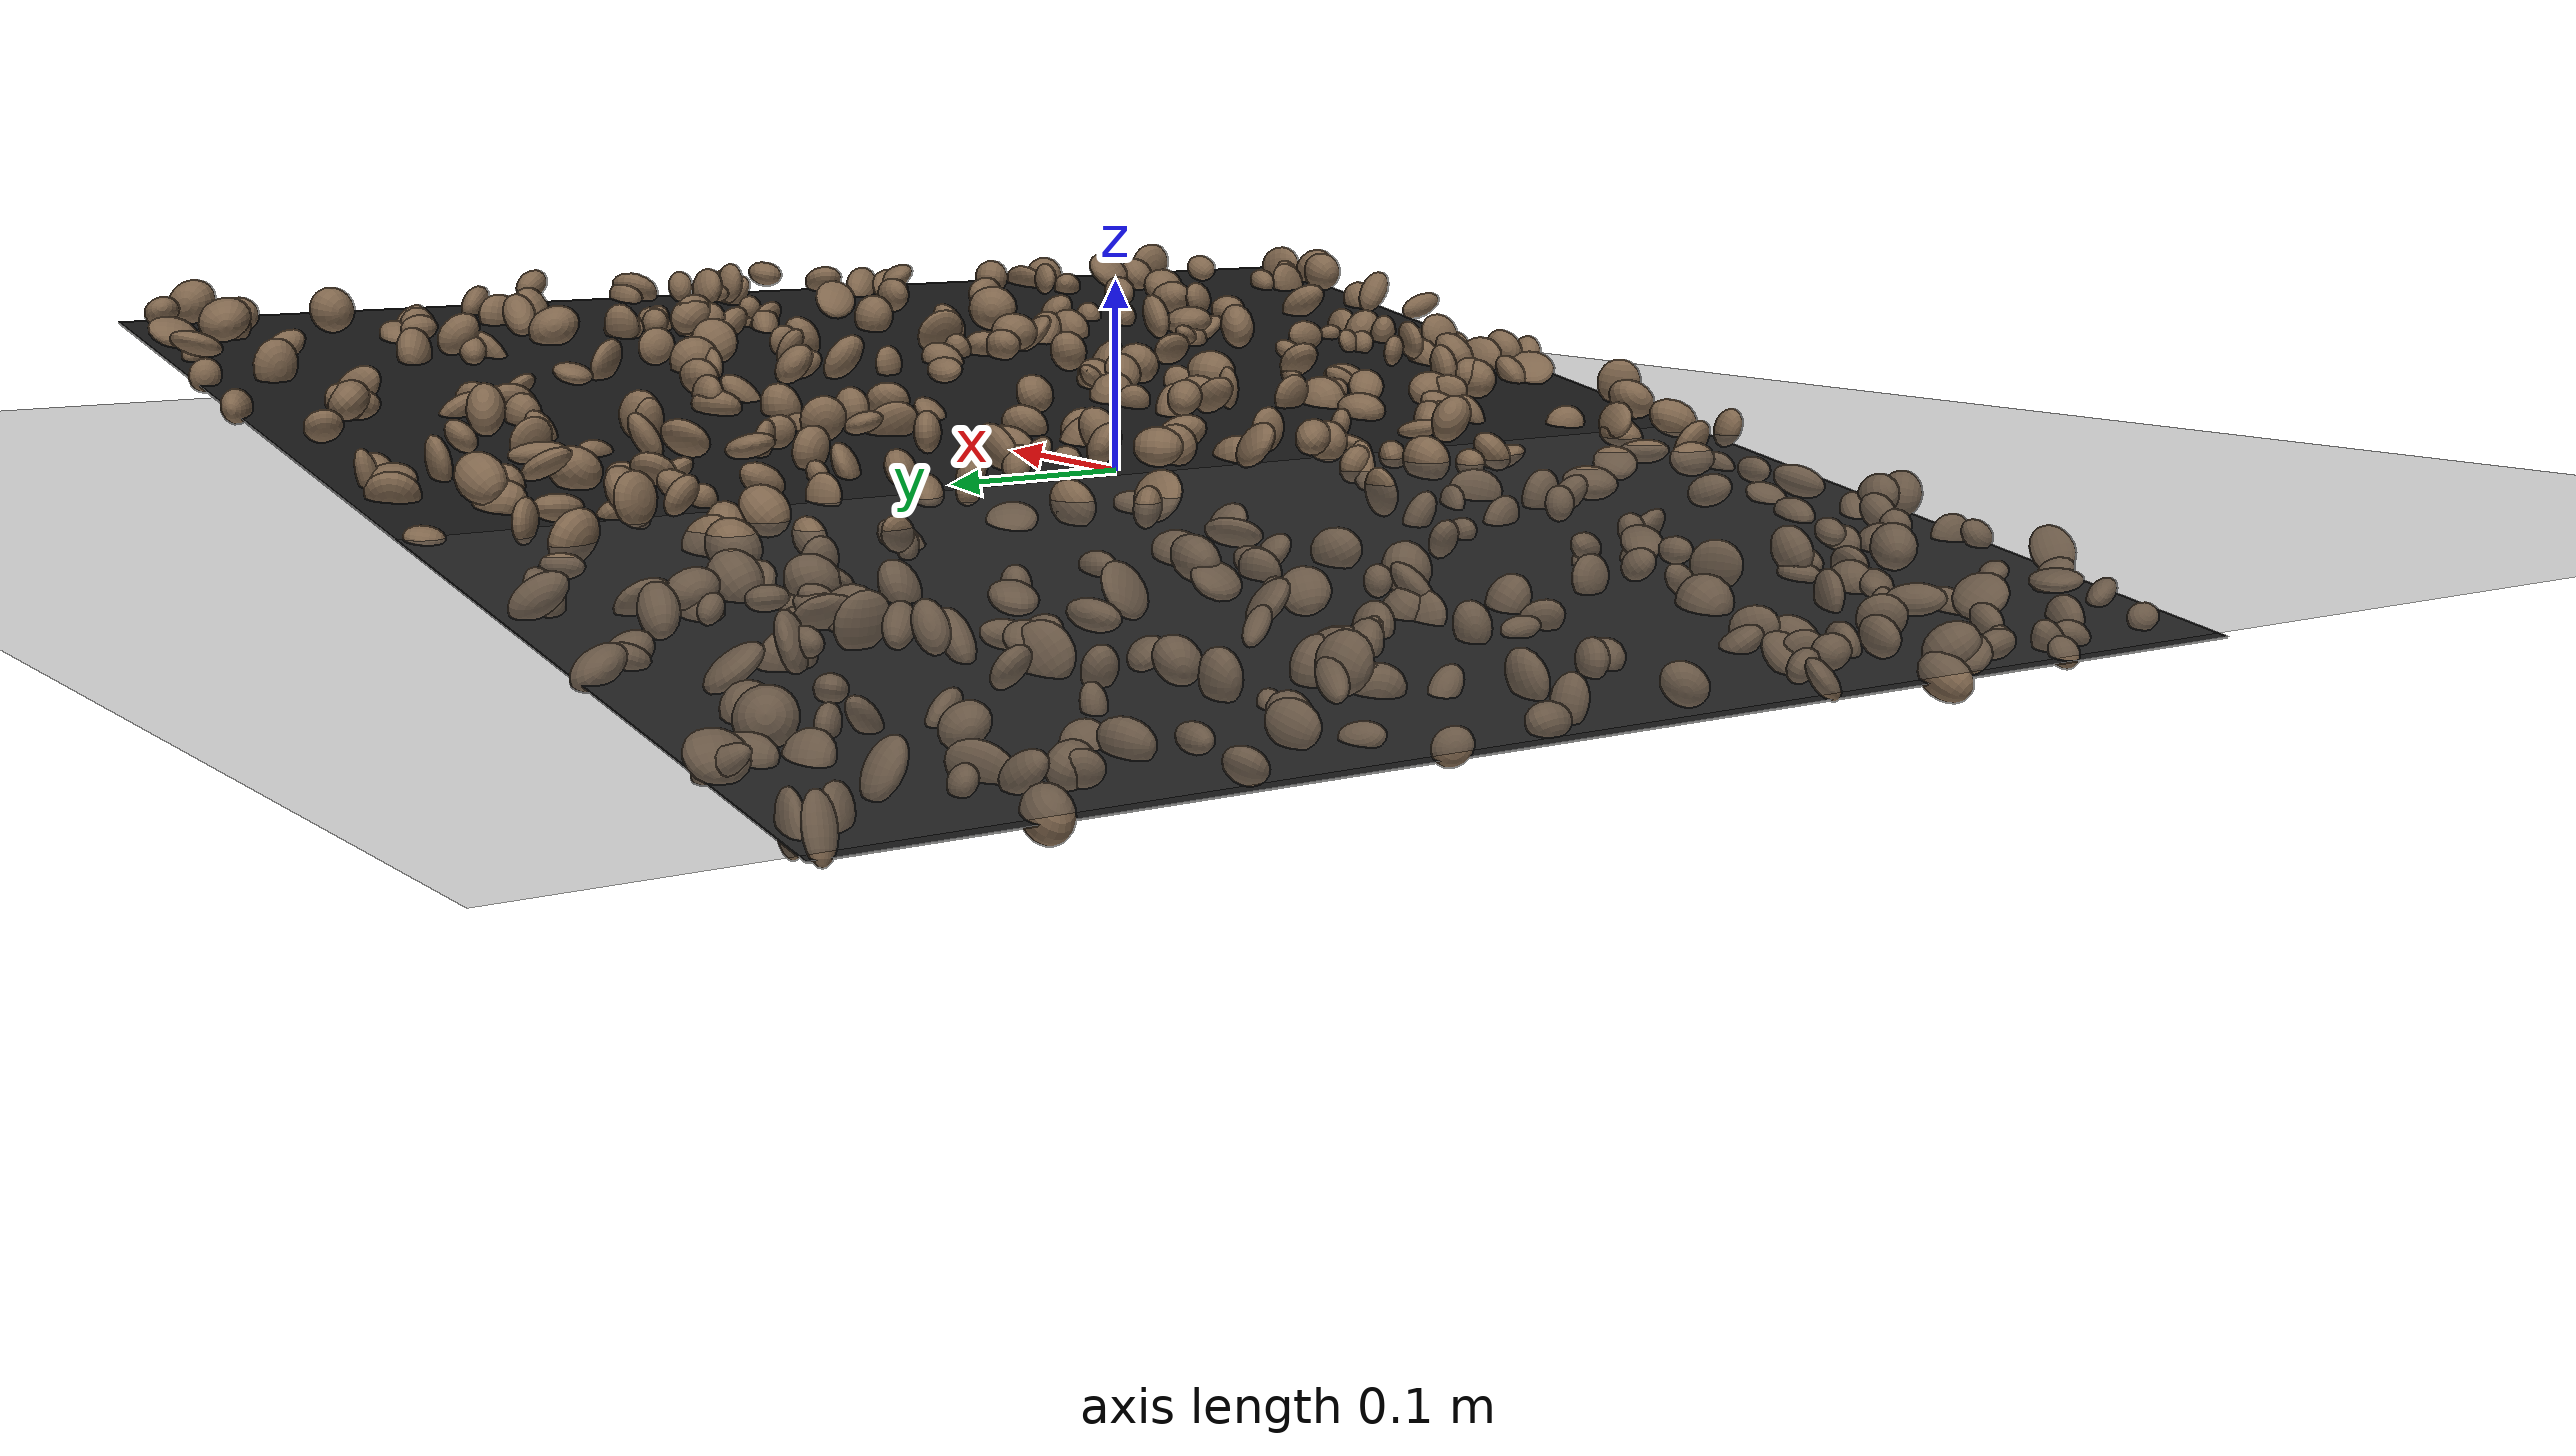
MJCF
<mujoco model="rocky_terrain_scene">
    <compiler angle="radian" inertiafromgeom="true" />
    <option timestep="0.002" gravity="0 0 -9.81" />

    <worldbody>
        <light name="sunlight" pos="5 5 5" dir="-1 -1 -1" diffuse="1 1 1" specular="0.5 0.5 0.5" ambient="0.5 0.5 0.5" />

        <geom name="ground_plane" type="plane" size="50 50 0.1" rgba="0.3 0.3 0.3 1" />

        <body name="rocky_terrain_body" axisangle="0 1 0 -0.17453292519943295">

        <geom name="rocky_terrain_plane" size="0.4 0.4 0.05" rgba="0.1 0.1 0.1 1" type="plane" /><geom name="rock1" type="ellipsoid" size="0.010345822399803122 0.012702377140176524 0.01164176661980915" pos="-0.39289135383811885 0.29229784444243534 0.0006631206235128001" quat="0.10400044906532645 0.38383253817354257 0.40228219437203994 0.10988481838909103" rgba="0.5 0.4 0.3 1" /><geom name="rock2" type="ellipsoid" size="0.007402415079824353 0.008500553957817545 0.012032001355438325" pos="-0.15528203686181552 -0.27718801289435196 0.013405016847896065" quat="0.1070585956530493 0.2166761307085956 0.41471997454312837 0.26154529909522667" rgba="0.5 0.4 0.3 1" /><geom name="rock3" type="ellipsoid" size="0.011616878597848448 0.014748756155881997 0.007224245971819403" pos="0.12898307494455474 -0.21427255121517705 0.014551227190865828" quat="0.40056649255746707 0.12149782115471548 0.19173714180318782 0.2861985444846296" rgba="0.5 0.4 0.3 1" /><geom name="rock4" type="ellipsoid" size="0.01048954271773057 0.005446642861300881 0.005950634432771131" pos="-0.2815740983150721 -0.03864578457040402 0.0033410546206061762" quat="0.33877091528810294 0.18777704777356072 0.2040104822322987 0.2694415547060376" rgba="0.5 0.4 0.3 1" /><geom name="rock5" type="ellipsoid" size="0.010661504829073645 0.01357973199513059 0.010454496756730512" pos="-0.2472177207491517 -0.06014700381943505 0.0033269581860347146" quat="0.20011993856512086 0.19889119084642437 0.2454984325785947 0.3554904380098601" rgba="0.5 0.4 0.3 1" /><geom name="rock6" type="ellipsoid" size="0.010931605098298625 0.00833214722299354 0.013666334965556696" pos="0.2356889596835079 -0.06174902561992057 0.004073711720104441" quat="0.328587016055025 0.43481857818159736 0.2275306987191198 0.009063707044257869" rgba="0.5 0.4 0.3 1" /><geom name="rock7" type="ellipsoid" size="0.014235514953949306 0.013217248811731287 0.007005057405570494" pos="0.1847039405483757 0.28788578927057107 0.0010790137661227577" quat="0.38302735673433347 0.06371336172944905 0.22102914202185717 0.3322301395143603" rgba="0.5 0.4 0.3 1" /><geom name="rock8" type="ellipsoid" size="0.013756993443180286 0.010493492220865694 0.008044803501869265" pos="0.30867090009858067 0.08604264037357368 0.006787398222010357" quat="0.3076309312678967 0.24058599223823476 0.38292639221083985 0.06885668428302862" rgba="0.5 0.4 0.3 1" /><geom name="rock9" type="ellipsoid" size="0.007483735774461497 0.005964203065099718 0.007347192447199398" pos="-0.36106457259236824 0.31126296980891144 0.004484687872295953" quat="0.4223009509211129 0.16046702952926192 0.40399231271840164 0.013239706831223537" rgba="0.5 0.4 0.3 1" /><geom name="rock10" type="ellipsoid" size="0.006888657825451257 0.008034848290459288 0.007323376330357691" pos="-0.2174788135699398 -0.003788699697297726 0.009065485572286728" quat="0.29859616686143725 0.2824387180182104 0.22256435571023525 0.196400759410117" rgba="0.5 0.4 0.3 1" /><geom name="rock11" type="ellipsoid" size="0.014217145254429762 0.01359922621126726 0.006097389818611734" pos="-0.24150118135295956 0.07936160247762913 0.01418188172921735" quat="0.07166823696111677 0.11485411815354525 0.2665867962862575 0.5468908485990804" rgba="0.5 0.4 0.3 1" /><geom name="rock12" type="ellipsoid" size="0.012026351528298864 0.013135357518197534 0.006417854851529066" pos="0.16937650846219032 -0.3548939945861008 0.013136736522696464" quat="0.29309606979644737 0.188518338340209 0.42720353385562393 0.09118205800771963" rgba="0.5 0.4 0.3 1" /><geom name="rock13" type="ellipsoid" size="0.013264066273853969 0.012850137144643541 0.006783450376575703" pos="0.18948700973280208 0.27757931518180556 0.001951917033629501" quat="0.38939980385066975 0.38265128068835047 0.018434778780965617 0.2095141366800142" rgba="0.5 0.4 0.3 1" /><geom name="rock14" type="ellipsoid" size="0.011901638256033978 0.014235226961266272 0.006908490531397614" pos="0.042697349864076695 0.24696675373633592 0.006425310228999747" quat="0.4982459797779231 0.2040981264534739 0.09063810522923746 0.2070177885393656" rgba="0.5 0.4 0.3 1" /><geom name="rock15" type="ellipsoid" size="0.014428147840160502 0.014348997528645466 0.008412291687542027" pos="-0.2117947094392113 0.3079646718043926 0.0025862694861602184" quat="0.2726462683298671 0.21390840290066127 0.2630413711982864 0.2504039575711851" rgba="0.5 0.4 0.3 1" /><geom name="rock16" type="ellipsoid" size="0.0135156905137036 0.013919939899405293 0.007207819583298871" pos="0.051388453408662105 0.3783821849971112 0.002759941920680132" quat="0.36816809770582853 0.23317071980961376 0.11043867469464395 0.2882225077899137" rgba="0.5 0.4 0.3 1" /><geom name="rock17" type="ellipsoid" size="0.012571188612195337 0.01379573553285807 0.006585260273970535" pos="-0.020224843694326533 0.2873929331444831 0.014231785938075557" quat="0.22351542585318956 0.19093777086862854 0.3539840827207624 0.23156272055741947" rgba="0.5 0.4 0.3 1" /><geom name="rock18" type="ellipsoid" size="0.01447647219501478 0.013386238859974715 0.012737828451048748" pos="0.2801373784318638 -0.0941301786156708 0.014447845681668346" quat="0.3222823685552616 0.325463460946908 0.2067332607532827 0.14552090974454773" rgba="0.5 0.4 0.3 1" /><geom name="rock19" type="ellipsoid" size="0.014433282460004096 0.006687507443256093 0.00924196510353528" pos="-0.06292044669704777 -0.3158109415904237 0.005700280308229145" quat="0.25521851346060553 0.3860785444896659 0.24263727397534965 0.11606566807437896" rgba="0.5 0.4 0.3 1" /><geom name="rock20" type="ellipsoid" size="0.006047821242813345 0.010164958233286312 0.005224109757028177" pos="0.06072672333756646 0.25596304298416694 0.0011827754266521134" quat="0.3979320480032921 0.17955411580106426 0.01167150363357237 0.4108423325620712" rgba="0.5 0.4 0.3 1" /><geom name="rock21" type="ellipsoid" size="0.014477818919090508 0.00579105220412832 0.01389831797434745" pos="-0.17501050993976675 0.27029647944685053 0.006281262394942761" quat="0.20984447602670825 0.43137596652330823 0.32238954924906404 0.036390008200919484" rgba="0.5 0.4 0.3 1" /><geom name="rock22" type="ellipsoid" size="0.011207702100606938 0.011021439908950555 0.014626125072111893" pos="-0.2394008908534124 -0.003322050758300499 0.00027264035571000766" quat="0.034027431680342154 0.4372610920998747 0.3962649853885004 0.13244649083128265" rgba="0.5 0.4 0.3 1" /><geom name="rock23" type="ellipsoid" size="0.013158614301748039 0.008768935610469795 0.012332250581453964" pos="0.07939141899399244 0.007451972001789098 0.00344915343253084" quat="0.05700711519726146 0.45653118787270813 0.2532321952498671 0.23322950168016332" rgba="0.5 0.4 0.3 1" /><geom name="rock24" type="ellipsoid" size="0.007896163490316205 0.006592800886020299 0.005900289526393988" pos="0.0036485015638039187 0.23861070309302812 0.0034020421110232085" quat="0.07796424084715038 0.3632227026994283 0.14777923556636555 0.4110338208870558" rgba="0.5 0.4 0.3 1" /><geom name="rock25" type="ellipsoid" size="0.013157840554516579 0.008705926532917022 0.013375469833162588" pos="0.2566476407234688 0.10566767912283215 0.010256088816696146" quat="0.40382490322661596 0.027347080108219596 0.20476665647173276 0.3640613601934317" rgba="0.5 0.4 0.3 1" /><geom name="rock26" type="ellipsoid" size="0.006208573997776265 0.010439682915224544 0.012125809302031453" pos="-0.32342447829713983 -0.14719202610557208 0.006240212525986072" quat="0.10277222023766644 0.22103587608438857 0.41868474237534653 0.25750716130259854" rgba="0.5 0.4 0.3 1" /><geom name="rock27" type="ellipsoid" size="0.007361643887164282 0.01208578806521447 0.00981866896032289" pos="0.3565396589539932 0.3506722922215266 0.005458377848727791" quat="0.12035302152320615 7.455446657039819e-05 0.41362299807400166 0.4659494259362218" rgba="0.5 0.4 0.3 1" /><geom name="rock28" type="ellipsoid" size="0.0064373625959867585 0.014248391995252584 0.012159955965824849" pos="-0.014935084363429663 -0.07822192656259103 0.012922165490686338" quat="0.32379253349617415 0.2707898357509994 0.06924562970431514 0.33617200104851125" rgba="0.5 0.4 0.3 1" /><geom name="rock29" type="ellipsoid" size="0.006367675611729091 0.014549601256398568 0.005241882420840057" pos="-0.059802941690830835 -0.11640411723661803 0.012031244228237398" quat="0.2804387635676381 0.474543167522147 0.23696521449227542 0.008052854417939608" rgba="0.5 0.4 0.3 1" /><geom name="rock30" type="ellipsoid" size="0.011787331253467969 0.008244084746675552 0.006480665619592511" pos="0.08874367253599474 -0.2082328704381766 0.0055368205743533076" quat="0.23089585992828662 0.3382119259690834 0.3648891375912115 0.06600307651141847" rgba="0.5 0.4 0.3 1" /><geom name="rock31" type="ellipsoid" size="0.007659555042404348 0.009118066127043786 0.014084411355765398" pos="0.20913946004931994 0.39922045486552016 0.0038460975138688274" quat="0.3229355751015871 0.302140236996677 0.2517327031172099 0.123191484784526" rgba="0.5 0.4 0.3 1" /><geom name="rock32" type="ellipsoid" size="0.012080368514758556 0.014843524828984895 0.013711281810885857" pos="0.12660114055817318 -0.0807474560385078 0.0010391439663131447" quat="0.17677686964913283 0.5892695812974529 0.1469392903207977 0.08701425873261658" rgba="0.5 0.4 0.3 1" /><geom name="rock33" type="ellipsoid" size="0.013446751758561613 0.01453609076312919 0.008775406023582259" pos="-0.061176550947407926 0.3373076289977056 0.012337806565354522" quat="0.04361521597436931 0.3300249276520623 0.1892646080464594 0.43709524832710894" rgba="0.5 0.4 0.3 1" /><geom name="rock34" type="ellipsoid" size="0.010651115281496582 0.007103200680212921 0.014380423553657085" pos="-0.13843346528069084 0.057196383722429356 0.005302414811633431" quat="0.3228906547573107 0.12788672279185356 0.35621011592779683 0.19301250652303883" rgba="0.5 0.4 0.3 1" /><geom name="rock35" type="ellipsoid" size="0.013504493777685839 0.007883921621621373 0.007017707377377513" pos="-0.39237066842695506 -0.23642303654576857 0.011662109135381165" quat="0.28433061386565567 0.1576501996971803 0.183947126993942 0.37407205944322186" rgba="0.5 0.4 0.3 1" /><geom name="rock36" type="ellipsoid" size="0.00508990897993919 0.007261445418710823 0.011399125177919201" pos="0.19821640932441498 0.26174354623471086 0.0020258275402404166" quat="0.06216789620424602 0.04776689542570882 0.5260807815025761 0.363984426867469" rgba="0.5 0.4 0.3 1" /><geom name="rock37" type="ellipsoid" size="0.005374697195054916 0.009241485031263777 0.010054167181086315" pos="0.35332610697745515 -0.17869384638470623 0.01182624075793592" quat="0.31731797624465563 0.21172546187876043 0.15800141682854477 0.31295514504803906" rgba="0.5 0.4 0.3 1" /><geom name="rock38" type="ellipsoid" size="0.012283714267112665 0.010031633840080899 0.005622920016859646" pos="0.05595687168455454 -0.2682236392648354 0.011228899825331012" quat="0.3689191593613328 0.3444134949966806 0.22481167204993163 0.061855673592054974" rgba="0.5 0.4 0.3 1" /><geom name="rock39" type="ellipsoid" size="0.006262781617004174 0.014005825044276617 0.008175327739358631" pos="0.0770443093443191 0.2354297473675695 0.013456876758166456" quat="0.29774201537073225 0.22454856951154337 0.3368789008571456 0.14083051426057874" rgba="0.5 0.4 0.3 1" /><geom name="rock40" type="ellipsoid" size="0.012006366814891914 0.008109064449382638 0.013919848180613117" pos="0.15584012897303012 0.15489993460226026 0.00310727710296487" quat="0.05794213752299595 0.2656230389261219 0.3094348493625551 0.3669999741883271" rgba="0.5 0.4 0.3 1" /><geom name="rock41" type="ellipsoid" size="0.013077968941496362 0.01185776709408579 0.005802492959921566" pos="0.08769673239333448 -0.17920198490085745 0.006963368979606901" quat="0.1982337466695667 0.2349078849423253 0.24055150543326245 0.3263068629548455" rgba="0.5 0.4 0.3 1" /><geom name="rock42" type="ellipsoid" size="0.010148090100563861 0.013803244729399651 0.0054895188436787" pos="0.043173446164912754 0.3043347088589605 0.014278514810620369" quat="0.19360456337051055 0.1582136104127626 0.1349607158825794 0.5132211103341474" rgba="0.5 0.4 0.3 1" /><geom name="rock43" type="ellipsoid" size="0.013967033843632962 0.00848715415399379 0.012682554734584243" pos="-0.3133777029267686 0.3928215499482325 0.007607186055437658" quat="0.31854792063016435 0.20731297089842432 0.15169779082344825 0.3224413176479631" rgba="0.5 0.4 0.3 1" /><geom name="rock44" type="ellipsoid" size="0.013379965715159786 0.006712970482784182 0.013073546849934309" pos="0.06856904031470779 0.21738784626956975 0.013936007358720632" quat="0.03806390982681692 0.3559565227243191 0.2490263973034363 0.3569531701454277" rgba="0.5 0.4 0.3 1" /><geom name="rock45" type="ellipsoid" size="0.012027954088518276 0.010938954150039053 0.011405446800704988" pos="0.3932805017318175 -0.2040664690381253 0.0036965740159897215" quat="0.42359046125412153 0.01622994971527866 0.03705576184216275 0.5231238271884371" rgba="0.5 0.4 0.3 1" /><geom name="rock46" type="ellipsoid" size="0.0120772279510316 0.010817661114914504 0.009024792887795823" pos="0.10525189865150175 -0.01439735013626342 0.012769745906631559" quat="0.0767032743889339 0.335815341651295 0.3396363117445985 0.24784507221517252" rgba="0.5 0.4 0.3 1" /><geom name="rock47" type="ellipsoid" size="0.006466294880154338 0.0050527232519586894 0.01259663342284643" pos="0.21746992330150228 -0.1946378537956469 0.008765127342884857" quat="0.27792980803849904 0.46204907459387773 0.08826789592845076 0.17175322143917243" rgba="0.5 0.4 0.3 1" /><geom name="rock48" type="ellipsoid" size="0.010469304668463483 0.006832752364955003 0.0055552389067434925" pos="-0.3700523019804317 0.12302025943805917 0.0024122354531379907" quat="0.23439290319976255 0.5029417424572311 0.23667109863474103 0.025994255708265364" rgba="0.5 0.4 0.3 1" /><geom name="rock49" type="ellipsoid" size="0.00977812644380837 0.006187420730801349 0.009278115270758044" pos="-0.08442303577146593 -0.3533901821224422 0.0005219113905984646" quat="0.10967111808150906 0.5261856021431299 0.19015099460255255 0.17399228517280835" rgba="0.5 0.4 0.3 1" /><geom name="rock50" type="ellipsoid" size="0.01049775499792941 0.01172760598039841 0.010232076061259796" pos="0.3614426415713342 0.34625096342309514 0.010630427890276323" quat="0.19399963028664652 0.2320694841856854 0.04031594171229248 0.5336149438153757" rgba="0.5 0.4 0.3 1" /><geom name="rock51" type="ellipsoid" size="0.006683660797935816 0.013449520817838758 0.007096935694814267" pos="-0.20731397663882378 -0.14337073415431772 0.010400505710589116" quat="0.5403950955820984 0.026056445740034306 0.25774077013783503 0.17580768854003226" rgba="0.5 0.4 0.3 1" /><geom name="rock52" type="ellipsoid" size="0.010229771998532942 0.0060418007482190795 0.011135357142992058" pos="-0.25592607372662834 -0.24564374320574178 0.001858341651587015" quat="0.0750804300301265 0.15317524795354723 0.3628575597348467 0.4088867622814796" rgba="0.5 0.4 0.3 1" /><geom name="rock53" type="ellipsoid" size="0.013705602361506 0.013529123887617605 0.008748087881819572" pos="0.3108280748890653 0.0920367466651057 0.010147000443762636" quat="0.08370167540532525 0.3617359495053041 0.155990000309465 0.3985723747799056" rgba="0.5 0.4 0.3 1" /><geom name="rock54" type="ellipsoid" size="0.014395740892580031 0.014075009507754182 0.011062151903074188" pos="-0.3008072181070698 0.094824442860095 0.006719461731697997" quat="0.3707464254961998 0.04929943324459518 0.39038815519689335 0.18956598606231165" rgba="0.5 0.4 0.3 1" /><geom name="rock55" type="ellipsoid" size="0.006483364553544555 0.006630655567345799 0.011139841588004589" pos="-0.3740596783539356 0.2122428962224533 0.014634365450382124" quat="0.15245360339536937 0.3814211740438151 0.1488542380676745 0.31727098449314106" rgba="0.5 0.4 0.3 1" /><geom name="rock56" type="ellipsoid" size="0.005057189807352742 0.01188448917243115 0.009408215302688469" pos="-0.00770840488155472 0.17907628743174553 0.002942951912402838" quat="0.12572240665268167 0.19795517493067868 0.34333811764972233 0.3329843007669174" rgba="0.5 0.4 0.3 1" /><geom name="rock57" type="ellipsoid" size="0.011987289275283235 0.010481881634678397 0.014706103009857661" pos="-0.17574887759246627 0.07335911089743596 0.014166083871609678" quat="0.14417990736632436 0.3953550726849232 0.11151096193095873 0.3489540580177938" rgba="0.5 0.4 0.3 1" /><geom name="rock58" type="ellipsoid" size="0.006848952946394462 0.007778319512694587 0.008351521408900177" pos="0.18960657101784695 -0.3098065497133137 0.004161431174719725" quat="0.2595107262027284 0.2759114643537259 0.11168242173794596 0.35289538770559964" rgba="0.5 0.4 0.3 1" /><geom name="rock59" type="ellipsoid" size="0.013709864705933786 0.013601791149762302 0.006238848484672002" pos="0.3240634562594772 0.03825686336544465 0.001891966671194456" quat="0.3145867822298 0.06721882506172157 0.28153516287519 0.33665922983328844" rgba="0.5 0.4 0.3 1" /><geom name="rock60" type="ellipsoid" size="0.008473941821291481 0.012729073762435547 0.006137531095455295" pos="-0.17807773456627318 -0.07540970199719454 0.011050089893766112" quat="0.34453091640213923 0.1036912733957326 0.27919350610009364 0.27258430410203466" rgba="0.5 0.4 0.3 1" /><geom name="rock61" type="ellipsoid" size="0.012205206980999785 0.008499185945084533 0.009566997180183511" pos="-0.18173870129317715 0.36704106740669595 0.0015832229165237421" quat="0.305340150833836 0.21880375267532648 0.3333677130742705 0.14248838341656714" rgba="0.5 0.4 0.3 1" /><geom name="rock62" type="ellipsoid" size="0.0055418527301635745 0.014227389899650725 0.013178869115744462" pos="-0.2523286415213691 -0.1897830027118606 0.010302796589829319" quat="0.17097317907646745 0.11631255538090823 0.37801843493431525 0.33469583060830915" rgba="0.5 0.4 0.3 1" /><geom name="rock63" type="ellipsoid" size="0.00773850833697046 0.011765388901949614 0.01482675671850437" pos="-0.3474256768532475 -0.18263465318188496 0.0014482962023843588" quat="0.27110789021308607 0.360620016319337 0.27894002032010556 0.08933207314747144" rgba="0.5 0.4 0.3 1" /><geom name="rock64" type="ellipsoid" size="0.012147322350324632 0.006719159627307439 0.006750030345253512" pos="-0.2217303391139785 0.20592153275056446 0.006227301776542175" quat="0.0981398006079484 0.44234512866592907 0.3369004603088612 0.12261461041726145" rgba="0.5 0.4 0.3 1" /><geom name="rock65" type="ellipsoid" size="0.007584309653484087 0.007625268962476506 0.008349666941415687" pos="-0.07192064289707989 -0.18026652268857 0.011794446746447224" quat="0.2110636523608849 0.31094987895083265 0.20146290734681183 0.27652356134147055" rgba="0.5 0.4 0.3 1" /><geom name="rock66" type="ellipsoid" size="0.013491083539477002 0.009190894382500772 0.00622444432907121" pos="0.18989393140169641 -0.2654277539349271 0.011214067392149118" quat="0.18007130829582932 0.28316290023837215 0.28640922209669034 0.2503565693691083" rgba="0.5 0.4 0.3 1" /><geom name="rock67" type="ellipsoid" size="0.008113219545651825 0.010547519194047627 0.006282642052550771" pos="-0.31420678538001534 -0.3692506046820281 0.009850970070812707" quat="0.08914741702758726 0.03869843537039978 0.16124553382911036 0.7109086137729026" rgba="0.5 0.4 0.3 1" /><geom name="rock68" type="ellipsoid" size="0.0074238470453847575 0.010694790865918149 0.007810023852990518" pos="0.0106197665066331 0.055425959072765596 0.005065379590958507" quat="0.09947725818261478 0.336931958754877 0.2819426347026466 0.2816481483598616" rgba="0.5 0.4 0.3 1" /><geom name="rock69" type="ellipsoid" size="0.014451617256778494 0.011253983115470025 0.012266355401582035" pos="0.23194731096984478 -0.07997276078222726 0.012359505930935646" quat="0.2213447639352538 0.24243773163599355 0.257253804886387 0.2789636995423657" rgba="0.5 0.4 0.3 1" /><geom name="rock70" type="ellipsoid" size="0.013311849344258258 0.00775291444229859 0.008352402039579373" pos="0.05229565349578519 0.03308199617166546 0.003441977677295156" quat="0.46668613894685557 0.28217322394223976 0.04062551058337737 0.21051512652752738" rgba="0.5 0.4 0.3 1" /><geom name="rock71" type="ellipsoid" size="0.0073371019610042835 0.011584658140892847 0.005541857817848079" pos="0.033910366473668685 -0.26972730961918767 0.005276986706503464" quat="0.15797763448808924 0.18279884903933974 0.4618702168170549 0.1973532996555161" rgba="0.5 0.4 0.3 1" /><geom name="rock72" type="ellipsoid" size="0.011942928892504227 0.008159012279083507 0.012339338887861104" pos="0.129304289185585 0.06490185256495318 0.006932168216521351" quat="0.05875102225747082 0.4513909936627587 0.3065899503138656 0.1832680337659049" rgba="0.5 0.4 0.3 1" /><geom name="rock73" type="ellipsoid" size="0.014198060057414905 0.01020699711152881 0.012445244213162503" pos="0.010531105886955772 -0.37213230635731914 0.012905274851842329" quat="0.16753556721479956 0.4438673018934993 0.17224009155343228 0.21635703933826883" rgba="0.5 0.4 0.3 1" /><geom name="rock74" type="ellipsoid" size="0.009169659948760223 0.010855918669806938 0.012833335467408738" pos="-0.2504207889931024 -0.2435768878531123 0.012886457842458557" quat="0.34652288199504166 0.09310550023900133 0.15492789313902106 0.40544372462693595" rgba="0.5 0.4 0.3 1" /><geom name="rock75" type="ellipsoid" size="0.00811086460633922 0.010291565715708967 0.005751738836753565" pos="-0.0005427003944440401 0.28900305042578 0.0015100586419297757" quat="0.3140296176845939 0.09064473984326034 0.17947954321117401 0.4158460992609717" rgba="0.5 0.4 0.3 1" /><geom name="rock76" type="ellipsoid" size="0.00905340959460764 0.014934641511978812 0.007903673912195914" pos="0.3358068829239492 0.1902655628685358 0.01011527501056916" quat="0.19088873176697635 0.4363545709965042 0.34868129678351417 0.024075400453005276" rgba="0.5 0.4 0.3 1" /><geom name="rock77" type="ellipsoid" size="0.009685537557580785 0.008501536658217417 0.005277742722268606" pos="-0.37744660504517535 0.26740593478467056 0.01019416181827696" quat="0.2746638339120215 0.30619369369892663 0.12201061125822632 0.29713186113082557" rgba="0.5 0.4 0.3 1" /><geom name="rock78" type="ellipsoid" size="0.010263904873692081 0.005028614500837393 0.012463226084503932" pos="0.3844912324006238 -0.18323552515565533 0.003728187057358145" quat="0.028024013885634254 0.423269336263851 0.21164304816876572 0.337063601681749" rgba="0.5 0.4 0.3 1" /><geom name="rock79" type="ellipsoid" size="0.007341784271537694 0.006565352219417552 0.009437268810039638" pos="-0.2180719098010723 0.302964275469748 0.012021576359558285" quat="0.1303814372367746 0.38387028136182155 0.1537673873877016 0.3319808940137023" rgba="0.5 0.4 0.3 1" /><geom name="rock80" type="ellipsoid" size="0.009543250795758466 0.01441984233009182 0.005292380614959383" pos="-0.10961233009591131 -0.08953424660635079 0.013897747423533975" quat="0.5004401463744258 0.3560353775271001 0.05081085473812034 0.09271362136035383" rgba="0.5 0.4 0.3 1" /><geom name="rock81" type="ellipsoid" size="0.01170691050180324 0.013386164773829975 0.007384865628139609" pos="0.09361649526543986 -0.29615987675147476 0.014961106856556725" quat="0.0158776165668315 0.1520578858369789 0.45792051877403817 0.3741439788221515" rgba="0.5 0.4 0.3 1" /><geom name="rock82" type="ellipsoid" size="0.012032345000661977 0.014930844159082749 0.010892860981193665" pos="0.15414575278563059 -0.08975870715774714 0.0016499479723340658" quat="0.12201802103389356 0.3192371945676168 0.39404572079606104 0.1646990636024286" rgba="0.5 0.4 0.3 1" /><geom name="rock83" type="ellipsoid" size="0.006273293104710451 0.01258161509036193 0.012697194765125475" pos="-0.29594050162688923 -0.2250117931790266 0.005993419655083239" quat="0.4172127199513634 0.17922792006701563 0.14168727530002218 0.2618720846815988" rgba="0.5 0.4 0.3 1" /><geom name="rock84" type="ellipsoid" size="0.010675245264370222 0.006412975069018063 0.007394719729523986" pos="-0.1636272100497192 0.26710505373916027 0.008648467951962903" quat="0.06508434095111297 0.4082327393608373 0.2697152602343636 0.25696765945368616" rgba="0.5 0.4 0.3 1" /><geom name="rock85" type="ellipsoid" size="0.011340811430200902 0.008916937011942013 0.00621208309659679" pos="0.18320603933384572 -0.0035451107314927732 0.006555389522064404" quat="0.16204670610018684 0.7518703488521447 0.07116066321915336 0.014922281828515089" rgba="0.5 0.4 0.3 1" /><geom name="rock86" type="ellipsoid" size="0.009309854310717127 0.012826526573655097 0.01028976110165692" pos="-0.1399406762131496 0.31719286643592004 0.011276404020913613" quat="0.07312637977705924 0.45090028814402117 0.05352539246142919 0.42244793961749044" rgba="0.5 0.4 0.3 1" /><geom name="rock87" type="ellipsoid" size="0.01114262145588165 0.013223779184517066 0.013061285097030327" pos="0.26450334193218794 -0.1410851123234193 0.0021391343720358258" quat="0.2008910576412312 0.2920645073330336 0.3889546651510661 0.11808976987466915" rgba="0.5 0.4 0.3 1" /><geom name="rock88" type="ellipsoid" size="0.012839728796716441 0.007848763916813991 0.013192220604435968" pos="-0.20956323682849132 -0.17895942768667963 0.004093164356448864" quat="0.030627831001960353 0.20503821333097386 0.5761479654877214 0.18818599017934431" rgba="0.5 0.4 0.3 1" /><geom name="rock89" type="ellipsoid" size="0.006754410925250778 0.011567912378449948 0.009746181116017875" pos="0.13222452448646438 0.26685769744135346 0.003658600988183702" quat="0.3487740070245446 0.24406703964767656 0.3036062232906016 0.10355273003717724" rgba="0.5 0.4 0.3 1" /><geom name="rock90" type="ellipsoid" size="0.005226253064054243 0.007079059777029131 0.013574651335932622" pos="-0.20097755677871057 -0.15082159387795607 0.0023830094149587216" quat="0.3842267005797538 0.4239579318519863 0.008319319251392171 0.18349604831686764" rgba="0.5 0.4 0.3 1" /><geom name="rock91" type="ellipsoid" size="0.009905328497660744 0.006566711529960559 0.0052985374595210626" pos="0.18839009240450644 0.08383764830487805 0.013207805241225966" quat="0.31479981008127567 0.20581820400960488 0.33025696425947204 0.14912502164964733" rgba="0.5 0.4 0.3 1" /><geom name="rock92" type="ellipsoid" size="0.013585449673732649 0.007254559568348303 0.009123661173819943" pos="-0.22917097989241617 0.16536647199840737 0.013293649359897713" quat="0.2989270666338156 0.5247781006228215 0.12786136938282278 0.048433463360540094" rgba="0.5 0.4 0.3 1" /><geom name="rock93" type="ellipsoid" size="0.005729730149508179 0.007028612772992898 0.01471761288881944" pos="-0.3284013875703691 0.10829312759458676 0.011315372289833732" quat="0.24181093302332815 0.3138537641358444 0.0799030544676415 0.364432248373186" rgba="0.5 0.4 0.3 1" /><geom name="rock94" type="ellipsoid" size="0.0075635769763797225 0.007255696829722373 0.010141044111359198" pos="0.27918289449918443 0.24243548011462612 0.0066127523317649605" quat="0.20015351714649743 0.32674650927559973 0.07690350993663492 0.3961964636412679" rgba="0.5 0.4 0.3 1" /><geom name="rock95" type="ellipsoid" size="0.005627683821039893 0.006084916393920708 0.00797280269555221" pos="-0.16531447096187596 0.32086862398916305 0.010994532612664172" quat="0.45934115863414837 0.26734134752306926 0.09587531855784445 0.17744217528493794" rgba="0.5 0.4 0.3 1" /><geom name="rock96" type="ellipsoid" size="0.0073552481839673015 0.005804454717874551 0.006322657423693801" pos="-0.14532968387159323 0.2716868577177508 6.229561676457883e-05" quat="0.042764071913291624 0.2754175818281082 0.24121940858775237 0.44059893767084785" rgba="0.5 0.4 0.3 1" /><geom name="rock97" type="ellipsoid" size="0.009090834027604553 0.007994832426847388 0.012131318346286326" pos="0.10308817862594488 -0.12676394804351515 0.008155506269949774" quat="0.22832491315400485 0.14707867160982704 0.28450021643310414 0.34009619880306396" rgba="0.5 0.4 0.3 1" /><geom name="rock98" type="ellipsoid" size="0.011891321880227752 0.009839769666438769 0.014448192307464195" pos="0.0304417807152923 0.3434802002349361 0.013995697208048302" quat="0.3999301404681576 0.07315985860498012 0.2918865243283692 0.2350234765984931" rgba="0.5 0.4 0.3 1" /><geom name="rock99" type="ellipsoid" size="0.011082000375979164 0.010166959150411811 0.006659638545622427" pos="0.2538329861861247 0.14341400404616333 0.010122394226021446" quat="0.2941194496153165 0.195759494024184 0.3959951656260139 0.11412589073448562" rgba="0.5 0.4 0.3 1" /><geom name="rock100" type="ellipsoid" size="0.007315711852938215 0.010605038451453448 0.007169281121997641" pos="-0.14665371129016613 -0.11380023876257556 0.0013591115364826334" quat="0.3945631789367403 0.10505419849250404 0.14189552886018278 0.35848709371057286" rgba="0.5 0.4 0.3 1" /><geom name="rock101" type="ellipsoid" size="0.005099739733439923 0.008756567920746939 0.009499399571309323" pos="-0.10186597900594363 -0.14493732826803107 0.0016764429611957736" quat="0.3217447894863128 0.2262180147482923 0.1651491864347274 0.28688800933066744" rgba="0.5 0.4 0.3 1" /><geom name="rock102" type="ellipsoid" size="0.009344738250146836 0.006667120195313423 0.009922556109963636" pos="-0.01618135610901561 0.09961617754936058 0.01128763879054246" quat="0.2182146849285814 0.22189708933068572 0.45857048420990837 0.10131774153082453" rgba="0.5 0.4 0.3 1" /><geom name="rock103" type="ellipsoid" size="0.010618989085291942 0.014715282193284548 0.011004160859591347" pos="0.02627538101691379 0.33502550765945394 0.001912044047999617" quat="0.3031230188470972 0.24031458971062755 0.01593672067596388 0.4406256707663114" rgba="0.5 0.4 0.3 1" /><geom name="rock104" type="ellipsoid" size="0.010863078792054778 0.008227728711388292 0.014936905126040644" pos="0.2756151400417276 -0.3278805185787464 0.008916052974704014" quat="0.02889224915543005 0.3546193018167503 0.38880045749144865 0.22768799153637106" rgba="0.5 0.4 0.3 1" /><geom name="rock105" type="ellipsoid" size="0.008632570779643184 0.007570825112578796 0.010932174234879896" pos="-0.08386908271094945 0.22852728419500967 0.00988287033039443" quat="0.6133687849616897 0.0005471986990699856 0.3721442330392789 0.013939783299961499" rgba="0.5 0.4 0.3 1" /><geom name="rock106" type="ellipsoid" size="0.007521856669860326 0.011835376962188213 0.01165662420732227" pos="-0.3097809050091095 0.3503163896523157 0.0008218916248839964" quat="0.06318881628265963 0.3100222090869492 0.2868810367218234 0.33990793790856777" rgba="0.5 0.4 0.3 1" /><geom name="rock107" type="ellipsoid" size="0.014946799004685225 0.011437047381032638 0.009579716965021932" pos="0.17966596884566333 0.35185171256064673 0.0119631879803321" quat="0.08541564714804412 0.1066787574134929 0.231262307645306 0.5766432877931569" rgba="0.5 0.4 0.3 1" /><geom name="rock108" type="ellipsoid" size="0.014486353924500237 0.00790442217633868 0.008789530955058317" pos="0.136196698370614 -0.37329215509610186 0.00034505951341884335" quat="0.34133602283544223 0.34183043913492694 0.013506395721182562 0.3033271423084482" rgba="0.5 0.4 0.3 1" /><geom name="rock109" type="ellipsoid" size="0.01400168622936369 0.01432571620124446 0.013918311987287622" pos="-0.2774246928545552 -0.15963104004389958 0.0023876419843014245" quat="0.47626439692488653 0.0524337147903408 0.45245163435858016 0.01885025392619253" rgba="0.5 0.4 0.3 1" /><geom name="rock110" type="ellipsoid" size="0.013411081485144489 0.009135108611974939 0.013475932559580926" pos="0.3472325855526266 0.1772695175999608 0.009538504667134226" quat="0.20349401713678475 0.014213206743577567 0.16239473708641267 0.619898039033225" rgba="0.5 0.4 0.3 1" /><geom name="rock111" type="ellipsoid" size="0.006034387078618797 0.013692149370508153 0.014990411571031863" pos="-0.08041788756300844 0.029624383361550266 0.012848377137325184" quat="0.2489937294096341 0.2658126836207922 0.07016776401622246 0.4150258229533513" rgba="0.5 0.4 0.3 1" /><geom name="rock112" type="ellipsoid" size="0.006172677856969574 0.012988519297275923 0.0076589867898141355" pos="-0.33649757651995327 -0.3796349249300744 0.004173293713698319" quat="0.027703491191982038 0.6096573056268466 0.15297722966128707 0.2096619735198843" rgba="0.5 0.4 0.3 1" /><geom name="rock113" type="ellipsoid" size="0.010975818689470212 0.005308695744135002 0.011174772216913192" pos="0.2223893876245443 0.20837028653656897 0.006507221799422461" quat="0.276524392909743 0.3059034224753675 0.18481943002566448 0.23275275458922492" rgba="0.5 0.4 0.3 1" /><geom name="rock114" type="ellipsoid" size="0.012458361190435578 0.007102546122779849 0.008500788626631004" pos="-0.27017841125122 0.060545715970252434 0.003154622074791048" quat="0.3142224496204907 0.23695969378612672 0.24739216739830094 0.20142568919508164" rgba="0.5 0.4 0.3 1" /><geom name="rock115" type="ellipsoid" size="0.012183144760439139 0.005122909548468515 0.014575312995513231" pos="-0.13671278010265758 0.24884553080872063 0.01009451520154162" quat="0.3312576971237563 0.5140033149905272 0.09215384077182454 0.06258514711389201" rgba="0.5 0.4 0.3 1" /><geom name="rock116" type="ellipsoid" size="0.013806135019874852 0.013453122597405016 0.011801830191112136" pos="0.23686119207609513 0.12811264054993332 0.0056857170526690625" quat="0.34260699802592 0.21878735219641776 0.263128522196712 0.17547712758095027" rgba="0.5 0.4 0.3 1" /><geom name="rock117" type="ellipsoid" size="0.0071730133045805064 0.009396426760855853 0.00680164850880843" pos="0.3746257734226677 0.06906801195853057 0.01208527433010598" quat="0.2618121406531432 0.4024411202079024 0.2621294693077932 0.07361726983116129" rgba="0.5 0.4 0.3 1" /><geom name="rock118" type="ellipsoid" size="0.009726303600447727 0.010017553096422237 0.007308594988125285" pos="-0.33556317286165344 -0.03419105989152882 0.0070919331223998835" quat="0.010639536283419602 0.1293419174484565 0.419944004800474 0.44007454146764985" rgba="0.5 0.4 0.3 1" /><geom name="rock119" type="ellipsoid" size="0.007675394529813514 0.011586440662560113 0.005212713006244147" pos="0.22252398108130322 0.0757782708159011 0.014339630767964632" quat="0.21949969008412626 0.170347182813117 0.23567241750785722 0.37448070959489954" rgba="0.5 0.4 0.3 1" /><geom name="rock120" type="ellipsoid" size="0.01138892633580407 0.011222625409603237 0.011752791740255213" pos="-0.2772432340390878 -0.2599275488276083 0.0027190424862726637" quat="0.015206124414211694 0.5643650321025769 0.109492033952345 0.3109368095308663" rgba="0.5 0.4 0.3 1" /><geom name="rock121" type="ellipsoid" size="0.007518791162120354 0.006172716150915758 0.007358247059496824" pos="0.025692226042771715 0.014257007617570427 0.0009951897654798668" quat="0.13296746868444212 0.1157780794451257 0.3733157846679086 0.37793866720252356" rgba="0.5 0.4 0.3 1" /><geom name="rock122" type="ellipsoid" size="0.012520465369833606 0.011505134432849708 0.011347281927279374" pos="0.30166066030919214 -0.023825919910283322 0.007525945679144731" quat="0.45162151958894303 0.0057091379126181325 0.4742488619683097 0.06842048053012921" rgba="0.5 0.4 0.3 1" /><geom name="rock123" type="ellipsoid" size="0.008778012936637124 0.013943396655321984 0.010841216680885763" pos="-0.30463472673686454 0.14977472752153886 0.00894596426794844" quat="0.2722121917023267 0.19860181529788998 0.27738842517212 0.2517975678276633" rgba="0.5 0.4 0.3 1" /><geom name="rock124" type="ellipsoid" size="0.005648285288086681 0.012471883504991874 0.013929822675796986" pos="0.37797217634753844 -0.3852553752133996 0.006670153234095358" quat="0.1354399812837272 0.2672039808157747 0.336493864537525 0.2608621733629731" rgba="0.5 0.4 0.3 1" /><geom name="rock125" type="ellipsoid" size="0.013896629303642313 0.006090955764333328 0.014649675783400665" pos="-0.18126235960160264 -0.207979778585581 0.004052076537515277" quat="0.047095968821327355 0.3262780170570077 0.5008990607940647 0.12572695332760028" rgba="0.5 0.4 0.3 1" /><geom name="rock126" type="ellipsoid" size="0.006699975078329266 0.011949864789634657 0.006928564367664413" pos="-0.14331610710652332 0.10609088137487677 0.0035513363931854607" quat="0.42577652026618645 0.05777235120272992 0.05607452850384765 0.460376600027236" rgba="0.5 0.4 0.3 1" /><geom name="rock127" type="ellipsoid" size="0.009282402961308212 0.010709716862355539 0.014972462775275218" pos="0.2560083047299522 -0.11701167741415991 0.004048524432269662" quat="0.36022233723252445 0.25452040771246975 0.0075293082643126535 0.3777279467906931" rgba="0.5 0.4 0.3 1" /><geom name="rock128" type="ellipsoid" size="0.007517747923748662 0.009352521297124225 0.006713951765301507" pos="-0.2351293766089353 -0.2860992422508757 0.014185443784265705" quat="0.03548321604365953 0.5309654691562677 0.40499664059766716 0.02855467420240554" rgba="0.5 0.4 0.3 1" /><geom name="rock129" type="ellipsoid" size="0.007108862762346627 0.007744686310942141 0.009320613924660968" pos="-0.24922726706929899 -0.13977982628786284 0.01450556423319822" quat="0.07190528718840014 0.3570834974842523 0.3748514788216595 0.19615973650568813" rgba="0.5 0.4 0.3 1" /><geom name="rock130" type="ellipsoid" size="0.0076230364366550035 0.007343379917934304 0.01012826436323835" pos="0.34990897177080205 -0.35010130350695523 0.003618699353598573" quat="0.23121581694527146 0.29962422878128847 0.15494628767448687 0.3142136665989531" rgba="0.5 0.4 0.3 1" /><geom name="rock131" type="ellipsoid" size="0.008472884373737935 0.009583476692500984 0.005949790730009876" pos="-0.398701266957953 0.09834745622690078 0.005370487283898697" quat="0.1857053587943358 0.4685489965569604 0.034037056311761474 0.3117085883369423" rgba="0.5 0.4 0.3 1" /><geom name="rock132" type="ellipsoid" size="0.014007040605976007 0.01396780000657133 0.00690305998785625" pos="0.36917420303626236 -0.2705742785327926 0.013658700772783297" quat="0.21185418112765803 0.27473254495026334 0.21841463181665433 0.29499864210542437" rgba="0.5 0.4 0.3 1" /><geom name="rock133" type="ellipsoid" size="0.007892707261124777 0.008853075769566027 0.011518745936692169" pos="-0.24085149150901428 -0.26214306227604134 0.0022070987294774335" quat="0.3284029188227291 0.05180808737520122 0.3626194415991828 0.2571695522028868" rgba="0.5 0.4 0.3 1" /><geom name="rock134" type="ellipsoid" size="0.005296136481971418 0.009787958664029787 0.01318572315897041" pos="-0.06362505227989068 0.2722249941946341 0.0073750959918886414" quat="0.02608185408963006 0.324609313692212 0.41054705075098274 0.23876178146717514" rgba="0.5 0.4 0.3 1" /><geom name="rock135" type="ellipsoid" size="0.0069874905635377085 0.010785069718533026 0.012432983330959137" pos="-0.3619742376632978 0.15374941703699452 0.008744816925877924" quat="0.16605708151790172 0.1828530821827541 0.26702587460235744 0.38406396169698687" rgba="0.5 0.4 0.3 1" /><geom name="rock136" type="ellipsoid" size="0.010277178136695816 0.012051950810989122 0.012918422965230925" pos="-0.18454612682264504 -0.37535907683540226 0.011216042574902187" quat="0.15207721673676974 0.4012638702116789 0.271732818587152 0.17492609446439938" rgba="0.5 0.4 0.3 1" /><geom name="rock137" type="ellipsoid" size="0.012359161998768981 0.006456730095036414 0.0073954045672838566" pos="-0.25411884574647925 0.3102331903078971 0.004473554101669112" quat="0.016506288076509237 0.19820903029115322 0.3556029246884731 0.4296817569438644" rgba="0.5 0.4 0.3 1" /><geom name="rock138" type="ellipsoid" size="0.007305250651384543 0.008823518230002268 0.006028468856702461" pos="-0.37362586240029566 -0.36599893352721397 0.005320513692121646" quat="0.10127845852249909 0.5998066712954333 0.0374976277851003 0.2614172423969674" rgba="0.5 0.4 0.3 1" /><geom name="rock139" type="ellipsoid" size="0.010655289645817655 0.005355492735920194 0.005414218391976474" pos="-0.16463944779822282 0.2734917020812957 0.0011690760520461868" quat="0.44004416457325457 0.35240440445420607 0.08480760019798035 0.122743830774559" rgba="0.5 0.4 0.3 1" /><geom name="rock140" type="ellipsoid" size="0.0068503846487562555 0.012785721236977281 0.01368712540502235" pos="-0.18019550983684304 0.25964911391004897 0.007813318675356139" quat="0.142889649868025 0.24401457024561812 0.1882218015774244 0.4248739783089324" rgba="0.5 0.4 0.3 1" /><geom name="rock141" type="ellipsoid" size="0.011538408877503493 0.005108682166754197 0.014279603803042523" pos="-0.29720420823714994 -0.3853439483139609 0.01452066518528437" quat="0.4732535701961885 0.13499269585355236 0.17329322323516896 0.21846051071509023" rgba="0.5 0.4 0.3 1" /><geom name="rock142" type="ellipsoid" size="0.006987713855455973 0.006553719009181943 0.010666996460897922" pos="-0.0160796621117959 -0.3333541424616492 0.004313071827299203" quat="0.0881429215419332 0.06070530148098043 0.013951610975384393 0.837200166001702" rgba="0.5 0.4 0.3 1" /><geom name="rock143" type="ellipsoid" size="0.0071860558101906405 0.00811020613613753 0.00810032743632522" pos="0.31880451165737167 0.11261530866551073 0.0061500074346252835" quat="0.1766626302989787 0.30724579122242873 0.2640218496248279 0.2520697288537647" rgba="0.5 0.4 0.3 1" /><geom name="rock144" type="ellipsoid" size="0.01281092687450066 0.00862551160780375 0.008621271353033534" pos="-0.38658926451750886 0.035645506718834485 0.00444929426141223" quat="0.3005821935305586 0.15859121619863797 0.13780078597355444 0.40302580429724894" rgba="0.5 0.4 0.3 1" /><geom name="rock145" type="ellipsoid" size="0.014510298455267818 0.0059318468788359035 0.013167104825242758" pos="0.3013134038542761 0.3894163697469819 0.012486536766609432" quat="0.1331453360493745 0.29902014424391576 0.2682278426579396 0.2996066770487701" rgba="0.5 0.4 0.3 1" /><geom name="rock146" type="ellipsoid" size="0.00521244785000283 0.0145944458833944 0.007750234665066606" pos="0.15155954171393127 -0.0835854870120829 0.005709828006900283" quat="0.4480397077536478 0.02229013887496466 0.2962782193252012 0.23339193404618638" rgba="0.5 0.4 0.3 1" /><geom name="rock147" type="ellipsoid" size="0.007041995642117001 0.01276191073894517 0.01489144810839068" pos="-0.0935761413373899 -0.167413194357973 0.002692435105405037" quat="0.0837801515620613 0.08691642934190062 0.3805159093738081 0.4487875097222301" rgba="0.5 0.4 0.3 1" /><geom name="rock148" type="ellipsoid" size="0.009374325252607061 0.008859785133084573 0.00653000539412383" pos="0.30040233967530694 0.24046409625192344 0.009382522237021554" quat="0.2627187817216104 0.21400557084917177 0.03470441507719499 0.48857123235202293" rgba="0.5 0.4 0.3 1" /><geom name="rock149" type="ellipsoid" size="0.0081732008964333 0.009646691382235634 0.014495976936464792" pos="0.3173186448677149 0.04109342993085685 0.0017522600495424917" quat="0.39233693219222715 0.22283935802935256 0.20915915448919128 0.1756645552892291" rgba="0.5 0.4 0.3 1" /><geom name="rock150" type="ellipsoid" size="0.013202579058385823 0.013704658814210301 0.0144818753151406" pos="-0.285753822670226 0.35718693180717753 0.008967028473790032" quat="0.19615571858972752 0.47758713148948767 0.08840444307097199 0.23785270684981288" rgba="0.5 0.4 0.3 1" /><geom name="rock151" type="ellipsoid" size="0.005551183769553586 0.011013433785125384 0.01364859735985241" pos="-0.30490938327178024 0.09294440572660684 0.013309694513657464" quat="0.026285652426307145 0.3772435791768992 0.39043312225408483 0.20603764614270872" rgba="0.5 0.4 0.3 1" /><geom name="rock152" type="ellipsoid" size="0.010320194006198177 0.009575568946703961 0.006000978066988483" pos="-0.16627245525497011 0.2944088585088803 0.013510855882225887" quat="0.30813275697632153 0.10964736263071648 0.055278308207267125 0.5269415721856949" rgba="0.5 0.4 0.3 1" /><geom name="rock153" type="ellipsoid" size="0.007387634230482779 0.007284191578060996 0.010286430989833789" pos="-0.06930334370398616 0.07440950088509551 0.006429831259496499" quat="0.13213412230979601 0.13990025093526567 0.20883344989596764 0.5191321768589706" rgba="0.5 0.4 0.3 1" /><geom name="rock154" type="ellipsoid" size="0.014677441646428424 0.005620236567411734 0.014237337915394555" pos="-0.2037398252850074 0.13208695075040977 0.013284422715594846" quat="0.32303399513366116 0.2579371341098291 0.037339746777111237 0.38168912397939847" rgba="0.5 0.4 0.3 1" /><geom name="rock155" type="ellipsoid" size="0.012063261664422648 0.009818642917533368 0.013552369330458686" pos="0.33112277706139437 -0.2556170463294626 0.009188783058505236" quat="0.4215244682047633 0.3852892424641794 0.00872134817534547 0.18446494115571183" rgba="0.5 0.4 0.3 1" /><geom name="rock156" type="ellipsoid" size="0.008631964014034066 0.010581943369524054 0.013411400022303954" pos="-0.3472934986323078 0.22604514236982132 0.00527529424774462" quat="0.25251783786518806 0.13787719717397082 0.35631541312914256 0.25328955183169866" rgba="0.5 0.4 0.3 1" /><geom name="rock157" type="ellipsoid" size="0.008771497549952812 0.01315227028653481 0.012559108619026559" pos="-0.25366632626256724 0.026233054117045018 0.001071977302061145" quat="0.4868100621708457 0.11270736545586682 0.01874450230240794 0.3817380700708794" rgba="0.5 0.4 0.3 1" /><geom name="rock158" type="ellipsoid" size="0.0062672794110956165 0.014695731030272226 0.012675196781833206" pos="-0.2466824333186981 -0.006268345725568114 0.0009797544249706901" quat="0.31951485104541166 0.11923115346178573 0.07876689255785982 0.48248710293494274" rgba="0.5 0.4 0.3 1" /><geom name="rock159" type="ellipsoid" size="0.005820158414886357 0.01132219488702352 0.008760203971581962" pos="0.034401745744010004 0.027957027808343526 0.0008634420370754164" quat="0.2530724524053543 0.33656967725150216 0.11555963443951055 0.2947982359036331" rgba="0.5 0.4 0.3 1" /><geom name="rock160" type="ellipsoid" size="0.007302906618948682 0.007370659557464741 0.0101987183968262" pos="0.3061383993175564 0.26287028532236 0.013393522878732994" quat="0.02252589981978855 0.005166315678189653 0.5073360855183802 0.4649716989836416" rgba="0.5 0.4 0.3 1" /><geom name="rock161" type="ellipsoid" size="0.0061069008032955535 0.009444739033989555 0.005749773730704768" pos="-0.30176935539589445 0.21199345331005492 0.0033038953462143066" quat="0.1832428094031891 0.25704809403374784 0.32674268134378204 0.23296641521928094" rgba="0.5 0.4 0.3 1" /><geom name="rock162" type="ellipsoid" size="0.007770223946078621 0.010626114036719266 0.013515356055897886" pos="0.20902761128666814 -0.34212768886879197 0.0036908296279738128" quat="0.17366438676240503 0.5269876859767804 0.2007056188006293 0.09864230846018544" rgba="0.5 0.4 0.3 1" /><geom name="rock163" type="ellipsoid" size="0.011034206275767795 0.01158889443993862 0.009043963236810424" pos="0.17204992725567503 -0.12506633016843527 0.004825314570976033" quat="0.18764321454198452 0.37130845677973157 0.0013291734855111902 0.43971915519277277" rgba="0.5 0.4 0.3 1" /><geom name="rock164" type="ellipsoid" size="0.012708193749229338 0.014973238206631753 0.009253895086557365" pos="0.06947329172276212 -0.023356187431622988 0.00017956810391077938" quat="0.347125203195089 0.1357814266252512 0.302879015410376 0.21421435476928385" rgba="0.5 0.4 0.3 1" /><geom name="rock165" type="ellipsoid" size="0.00997652804781167 0.006080214936674878 0.009278399923074231" pos="-0.27434750684377207 0.16772086288225607 0.01112254505803501" quat="0.0009431492305449581 0.08442057379578806 0.6236359008482109 0.2910003761254562" rgba="0.5 0.4 0.3 1" /><geom name="rock166" type="ellipsoid" size="0.011412327772541673 0.009247548385794469 0.009653139666468566" pos="-0.33166128264028727 0.2937150679481142 0.014694453358823594" quat="0.35994475313591995 0.21769962901837014 0.30761107225674666 0.11474454558896321" rgba="0.5 0.4 0.3 1" /><geom name="rock167" type="ellipsoid" size="0.008036177765485323 0.010554177929783628 0.011843893358126545" pos="0.3970145625489584 0.09391161417996807 0.0013344027057183366" quat="0.19164782522480012 0.2388709976430359 0.2950584055480839 0.2744227715840801" rgba="0.5 0.4 0.3 1" /><geom name="rock168" type="ellipsoid" size="0.009024606027736786 0.014928554160506764 0.006287472513414618" pos="0.2907940089801081 0.22633619174255848 0.00044557864010164646" quat="0.5393388526525484 0.3024766986511187 0.15055612744825467 0.007628321248078188" rgba="0.5 0.4 0.3 1" /><geom name="rock169" type="ellipsoid" size="0.01437711896366884 0.011529845749048634 0.01498512493058719" pos="0.34336072857720956 0.359854405736336 0.013635111402347652" quat="0.3365180261756391 0.2306276188045089 0.27775789316660476 0.15509646185324727" rgba="0.5 0.4 0.3 1" /><geom name="rock170" type="ellipsoid" size="0.009907644250664146 0.01280949205597292 0.01029101678076223" pos="0.17647568943639413 -0.08218116055170877 0.01492171758306676" quat="0.20336292558296473 0.04029631409936912 0.47192855336138584 0.28441220695628033" rgba="0.5 0.4 0.3 1" /><geom name="rock171" type="ellipsoid" size="0.010379613422936272 0.00946899831842601 0.009719817256309948" pos="-0.33950626791042765 0.13829798903297963 0.0035833397082981715" quat="0.3501049359859557 0.3310178232783759 0.05050965345902862 0.26836758727663984" rgba="0.5 0.4 0.3 1" /><geom name="rock172" type="ellipsoid" size="0.007184814070201441 0.011854592118704772 0.007595469227851821" pos="-0.37796696534437485 -0.30831526550696 0.0032848971332596353" quat="0.32334026248611847 0.06366035886540274 0.5016063156720901 0.11139306297638872" rgba="0.5 0.4 0.3 1" /><geom name="rock173" type="ellipsoid" size="0.012545529965923344 0.013419034421266213 0.014396163522635213" pos="-0.12158997681740324 0.2865134886460031 0.0067626887625868055" quat="0.3914535023751612 0.07668980233904706 0.22602182815218724 0.3058348671336045" rgba="0.5 0.4 0.3 1" /><geom name="rock174" type="ellipsoid" size="0.011119485828907493 0.008467844027364727 0.006577912644324866" pos="-0.378953753693853 -0.12300466361283852 0.008909721058198825" quat="0.23311304134885344 0.15109193831367376 0.2682140059128516 0.3475810144246212" rgba="0.5 0.4 0.3 1" /><geom name="rock175" type="ellipsoid" size="0.013208055471298514 0.013137682612216227 0.014569201920509929" pos="0.1331239180126189 -0.1540114404401888 0.009004258404992123" quat="0.14717857687924155 0.24793408963761923 0.2976167589426961 0.30727057454044304" rgba="0.5 0.4 0.3 1" /><geom name="rock176" type="ellipsoid" size="0.01236721033834486 0.005882615360747376 0.009640939068000693" pos="-0.2899747667343209 0.277611543008944 0.0029842919398160544" quat="0.18727178827135157 0.28172121953698254 0.5264125635711829 0.004594428620482923" rgba="0.5 0.4 0.3 1" /><geom name="rock177" type="ellipsoid" size="0.01157591463477935 0.012351749541732016 0.008372391493812999" pos="0.049539974205749515 0.1554845868339516 0.009387261735123465" quat="0.13878082581821286 0.2554076693153731 0.2702783276426656 0.33553317722374837" rgba="0.5 0.4 0.3 1" /><geom name="rock178" type="ellipsoid" size="0.013392446496594688 0.008967613121834262 0.010870925459743629" pos="0.06528496699786002 -0.262626474513481 0.011172251300042917" quat="0.2952799526117097 0.14637176742401906 0.25574987526403764 0.30259840470023364" rgba="0.5 0.4 0.3 1" /><geom name="rock179" type="ellipsoid" size="0.006399475904847807 0.01192922281475086 0.008418163581858183" pos="0.3701824371689173 0.03815545781309487 0.014039749380357359" quat="0.19171405616968534 0.24778097223506465 0.2780598088572628 0.28244516273798725" rgba="0.5 0.4 0.3 1" /><geom name="rock180" type="ellipsoid" size="0.011251495581004783 0.00784176362282312 0.011965616658561856" pos="0.1444355354498933 -0.09936984899667489 0.009935024234039743" quat="0.3609236746163375 0.23266553717407296 0.07221147115843324 0.3341993170511563" rgba="0.5 0.4 0.3 1" /><geom name="rock181" type="ellipsoid" size="0.012482006091944109 0.009080245428728987 0.007528868337417971" pos="-0.17851224031701093 -0.36615373670281726 0.001500499527086974" quat="0.1827862067534229 0.14707856664102814 0.5593291792522803 0.11080604735326868" rgba="0.5 0.4 0.3 1" /><geom name="rock182" type="ellipsoid" size="0.011434127035689131 0.011462818324978589 0.014392950083709343" pos="-0.3923499815248634 -0.20528466659138714 0.013489747262505266" quat="0.04080408427485505 0.20487165081861453 0.500022375169807 0.25430188973672346" rgba="0.5 0.4 0.3 1" /><geom name="rock183" type="ellipsoid" size="0.009498077428947429 0.009349556302754752 0.005393858292530723" pos="0.14346676684413784 -0.2978764090691165 0.012066850676258234" quat="0.14018825211534067 0.2015893905194705 0.3170829410711691 0.3411394162940198" rgba="0.5 0.4 0.3 1" /><geom name="rock184" type="ellipsoid" size="0.007266037407490376 0.01281756401300475 0.01300962958368082" pos="-0.11619143494224676 0.37576990578626057 0.0069982208983583915" quat="0.4448150301866756 0.14341580374662294 0.25127773597994635 0.16049143008675515" rgba="0.5 0.4 0.3 1" /><geom name="rock185" type="ellipsoid" size="0.009183422751713768 0.012518152792698606 0.013725671024211152" pos="0.2912421886665111 0.2714788834953161 0.004652505112358086" quat="0.43339680538376685 0.21506444179592638 0.17991055070178028 0.1716282021185265" rgba="0.5 0.4 0.3 1" /><geom name="rock186" type="ellipsoid" size="0.010634812142340832 0.013911001084703972 0.010856340196024043" pos="0.1432158664259061 0.1226143750114358 0.0037863392676244167" quat="0.23287406114990492 0.1223758189635476 0.3994194069792234 0.24533071290732414" rgba="0.5 0.4 0.3 1" /><geom name="rock187" type="ellipsoid" size="0.011896405321965668 0.011318043202885746 0.0071654999959404305" pos="0.24098626580369586 -0.3338902881249922 0.0011024655816921263" quat="0.029747937453771335 0.019268296076917973 0.43806818624273836 0.5129155802265725" rgba="0.5 0.4 0.3 1" /><geom name="rock188" type="ellipsoid" size="0.012526718285970039 0.01248557939130478 0.0071937035335856" pos="-0.33271362418901984 -0.22339192203483407 0.006260582413778415" quat="0.27604794428327495 0.3582995631284257 0.02602535811459239 0.33962713447370696" rgba="0.5 0.4 0.3 1" /><geom name="rock189" type="ellipsoid" size="0.006918857021787308 0.009999552588618177 0.007547253980492054" pos="0.018631350001884428 0.24691435652783078 0.006482380952180138" quat="0.39994822789648676 0.16411185702535866 0.3944786432586121 0.041461271819542546" rgba="0.5 0.4 0.3 1" /><geom name="rock190" type="ellipsoid" size="0.011404866114504907 0.008522605500800614 0.013265515216494706" pos="0.31499176192123046 -0.16368399001335876 0.0003040509018082682" quat="0.2302603776795024 0.24094742720403572 0.44784265315607036 0.08094954196039159" rgba="0.5 0.4 0.3 1" /><geom name="rock191" type="ellipsoid" size="0.006875131528313344 0.014116358779681856 0.008097940942343965" pos="0.1754487018294959 0.12968428900365037 0.0027006038784956076" quat="0.48461788066183126 0.22055593753647512 0.27628429882682604 0.01854188297486751" rgba="0.5 0.4 0.3 1" /><geom name="rock192" type="ellipsoid" size="0.008246036185544587 0.012390716191263331 0.00507585524563348" pos="-0.1031810039830175 0.1928286504700567 0.014449177307550484" quat="0.37535604431410174 0.08206468601320052 0.33607506714047575 0.20650420253222201" rgba="0.5 0.4 0.3 1" /><geom name="rock193" type="ellipsoid" size="0.014425288215294103 0.011945032167737691 0.005455393749231845" pos="-0.14591543401752743 0.029834429055465073 0.013790074453931836" quat="0.5175580080380916 0.18766979003890796 0.08728133564635387 0.20749086627664654" rgba="0.5 0.4 0.3 1" /><geom name="rock194" type="ellipsoid" size="0.0075829286392676346 0.0078125855418908 0.011928257774061281" pos="-0.05090407405537256 -0.12560521456314416 0.0014825876168583435" quat="0.40302689346066 0.0794924224145768 0.23660152913907523 0.2808791549856879" rgba="0.5 0.4 0.3 1" /><geom name="rock195" type="ellipsoid" size="0.008329491281236718 0.013069670763889239 0.008773386857883269" pos="0.12668750953804264 -0.3911028892994258 0.008519956511634933" quat="0.03836549076964858 0.33418624667582936 0.29763702927286 0.32981123328166206" rgba="0.5 0.4 0.3 1" /><geom name="rock196" type="ellipsoid" size="0.014586758815855538 0.009199714160899701 0.007886265361619623" pos="0.03035663113216619 -0.2347803411828876 0.005535434752166941" quat="0.187736943331611 0.061223372748233695 0.3198920806987709 0.43114760322138446" rgba="0.5 0.4 0.3 1" /><geom name="rock197" type="ellipsoid" size="0.009878093585591836 0.014910269593126586 0.013122131411474846" pos="-0.32087595227898985 0.09645884251935016 0.014854421130636066" quat="0.17979585456841107 0.2122061422366471 0.2610769254822508 0.346921077712691" rgba="0.5 0.4 0.3 1" /><geom name="rock198" type="ellipsoid" size="0.013148456485431202 0.006794762466481594 0.011426802528580558" pos="-0.1929085308741687 0.18447794120002325 0.011539555932336656" quat="0.08204138952495182 0.039794016975992996 0.4273472183285847 0.4508173751704704" rgba="0.5 0.4 0.3 1" /><geom name="rock199" type="ellipsoid" size="0.008493868428852571 0.00794046709776736 0.01420923618177252" pos="0.3655625658506214 -0.20437105396358293 0.0024693759419227067" quat="0.2973022323515345 0.3405722793629614 0.33370568149146884 0.02841980679403525" rgba="0.5 0.4 0.3 1" /><geom name="rock200" type="ellipsoid" size="0.008457127609992099 0.012695460301381757 0.013335110212292917" pos="-0.007853581153830391 0.287032124035284 0.01453992798261273" quat="0.40749277673570855 0.22955670374193224 0.25767347505051286 0.10527704447184637" rgba="0.5 0.4 0.3 1" /><geom name="rock201" type="ellipsoid" size="0.00982129988937604 0.008000559474303089 0.006856637761557367" pos="-0.2430183385033673 -0.39039660939840604 0.005781728600803232" quat="0.08522903746585292 0.4421463397765962 0.24936445431075077 0.2232601684468002" rgba="0.5 0.4 0.3 1" /><geom name="rock202" type="ellipsoid" size="0.01183989306505746 0.008275995033533021 0.010089575015760254" pos="0.15570977099801708 -0.3326781173469755 0.003087614047762039" quat="0.006757877960740432 0.6834751214507258 0.06012455680091006 0.2496424437876237" rgba="0.5 0.4 0.3 1" /><geom name="rock203" type="ellipsoid" size="0.007801250330161656 0.007432064685563192 0.013846668545638523" pos="0.3213240021614059 0.38184263019183695 0.003287179481932827" quat="0.4074204981119425 0.2670881488907482 0.2563239877112606 0.06916736528604868" rgba="0.5 0.4 0.3 1" /><geom name="rock204" type="ellipsoid" size="0.012927343547075091 0.005161464157190871 0.014347093236175237" pos="0.008009891368321198 -0.16024365669456542 0.0010425490332283377" quat="0.207242181071632 0.3505592766469559 0.2052922234557647 0.2369063188256474" rgba="0.5 0.4 0.3 1" /><geom name="rock205" type="ellipsoid" size="0.01068664801260215 0.014392884729499802 0.005521527926848345" pos="0.18241877695264663 -0.15997052476663579 0.010553751194921988" quat="0.4890723067731696 0.04135606342304264 0.3134513902405686 0.15612023956321905" rgba="0.5 0.4 0.3 1" /><geom name="rock206" type="ellipsoid" size="0.008129177768783028 0.009132511858897806 0.010780048267751146" pos="-0.20683103952152646 -0.3516539386443318 0.011102349442871954" quat="0.3213969977968786 0.1678955888698381 0.2180562600542397 0.2926511532790437" rgba="0.5 0.4 0.3 1" /><geom name="rock207" type="ellipsoid" size="0.008913446968515653 0.014937710391910924 0.008087277052271507" pos="-0.12463294088550836 0.38257398157144307 0.009457494481761258" quat="0.18158246119220228 0.3137776186376307 0.09686579188169758 0.40777412828846954" rgba="0.5 0.4 0.3 1" /><geom name="rock208" type="ellipsoid" size="0.0069756911101622725 0.00838105825948598 0.005889364040098557" pos="-0.39068397351167167 -0.23937246565788836 0.011621806090248031" quat="0.12679401548173597 0.33885015637033966 0.22123986004749965 0.31311596810042475" rgba="0.5 0.4 0.3 1" /><geom name="rock209" type="ellipsoid" size="0.014778649878124689 0.009931498590410828 0.010480556767305665" pos="-0.024682582706737954 -0.372989496223318 0.010939858127305168" quat="0.4833752000494783 0.18877478601689837 0.013483690715417931 0.3143663232182053" rgba="0.5 0.4 0.3 1" /><geom name="rock210" type="ellipsoid" size="0.010251725577894938 0.006935608690151232 0.0056259397451251395" pos="-0.09312687363303385 0.3573104396484643 0.010824476347056938" quat="0.4859692309925307 0.16128206974827958 0.10039192989334264 0.2523567693658471" rgba="0.5 0.4 0.3 1" /><geom name="rock211" type="ellipsoid" size="0.012029687855656196 0.006434952440521055 0.006489927664859925" pos="0.09815532368957242 0.25201839691938444 0.0005022936480190804" quat="0.1156872650306693 0.2710305822889432 0.32751059883685213 0.2857715538435354" rgba="0.5 0.4 0.3 1" /><geom name="rock212" type="ellipsoid" size="0.007922733443171655 0.008104458105101593 0.013185608377796011" pos="0.09096159965164896 0.3704676209577843 0.001486177910742098" quat="0.3863962623355899 0.15240276871329572 0.29933445308338 0.16186651586773437" rgba="0.5 0.4 0.3 1" /><geom name="rock213" type="ellipsoid" size="0.008023178367849326 0.012847280331477126 0.008037699962699917" pos="-0.2231174984121343 0.2453554350028696 0.014158999165077034" quat="0.26459587027393583 0.3667543956501995 0.2980767347902805 0.07057299928558412" rgba="0.5 0.4 0.3 1" /><geom name="rock214" type="ellipsoid" size="0.007138706736439172 0.012172091856314828 0.014826771771587022" pos="0.024011340486243593 0.05933713052862988 0.010276470759265582" quat="0.3264311137224467 0.1302988126058115 0.24123890656203553 0.30203116710970623" rgba="0.5 0.4 0.3 1" /><geom name="rock215" type="ellipsoid" size="0.013792431832052733 0.006023712676973782 0.014691402298558386" pos="-0.20267975644184066 0.2673222455642813 0.01215954555469234" quat="0.041570046868290446 0.4682744936704281 0.4709134706143982 0.019241988846883225" rgba="0.5 0.4 0.3 1" /><geom name="rock216" type="ellipsoid" size="0.005302011854575571 0.011114197750919442 0.013272820725957538" pos="-0.027817613013579323 -0.32468092192752096 0.013342789263507123" quat="0.24240422171000978 0.30299691893794894 0.14669973516816753 0.30789912418387383" rgba="0.5 0.4 0.3 1" /><geom name="rock217" type="ellipsoid" size="0.005710358911963604 0.00720168783762554 0.010694235105118337" pos="-0.12434290417812072 -0.34061152662659133 0.011157423672453183" quat="0.22647881083105156 0.2505833616623036 0.28852548366475045 0.23441234384189438" rgba="0.5 0.4 0.3 1" /><geom name="rock218" type="ellipsoid" size="0.010168719150706784 0.012487590276630605 0.005689439760435795" pos="0.008315096825274093 -0.10338179598642977 0.013231996139492592" quat="0.22213760088144655 0.27813118151841243 0.2578582668495576 0.24187295075058343" rgba="0.5 0.4 0.3 1" /><geom name="rock219" type="ellipsoid" size="0.014732901373584937 0.008619836031328928 0.007084404526935985" pos="-0.3322136664394817 -0.24616672858321556 0.013041834810880601" quat="0.19176661576609963 0.5465336810136259 0.2417606667942535 0.01993903642602096" rgba="0.5 0.4 0.3 1" /><geom name="rock220" type="ellipsoid" size="0.01005347984624719 0.013834359048467991 0.012759097253634347" pos="0.20908143664689838 -0.22688558603658493 0.014487048733842843" quat="0.200715314077106 0.4858797505144254 0.29046871415313996 0.0229362212553287" rgba="0.5 0.4 0.3 1" /><geom name="rock221" type="ellipsoid" size="0.008318895987120543 0.010722985152228474 0.014964722246560331" pos="0.38662032218795483 -0.06352631723433017 0.0035547176743954264" quat="0.49969674158259086 0.2489352714856594 0.20771247797456782 0.04365550895718192" rgba="0.5 0.4 0.3 1" /><geom name="rock222" type="ellipsoid" size="0.008198878488563089 0.00816026854025146 0.01172381131037441" pos="0.23472775658236367 -0.04292172422572127 0.0018923520458102615" quat="0.1246989529048145 0.7341394483252618 0.01070076388545514 0.1304608348844686" rgba="0.5 0.4 0.3 1" /><geom name="rock223" type="ellipsoid" size="0.006249810839468911 0.007797612102823053 0.011430712315305567" pos="0.11468845793891291 0.1264331828715336 0.00077178872177454" quat="0.1378558824084926 0.2558557487875076 0.34337567265309676 0.26291269615090296" rgba="0.5 0.4 0.3 1" /><geom name="rock224" type="ellipsoid" size="0.007880708543259358 0.01238412046445183 0.011526505983738531" pos="0.0023375737520013873 0.007740807214215717 0.014602760780255606" quat="0.4016459289375027 0.31998846244068324 0.03533512357911641 0.2430304850426976" rgba="0.5 0.4 0.3 1" /><geom name="rock225" type="ellipsoid" size="0.014117845096934818 0.00895745600128917 0.010752059292551554" pos="0.035181627976194285 -0.06599961134465782 0.006441538920761142" quat="0.19663609686248057 0.3876060307302611 0.3498175855485637 0.0659402868586947" rgba="0.5 0.4 0.3 1" /><geom name="rock226" type="ellipsoid" size="0.008825850650199526 0.0054619301031553595 0.010223675578332841" pos="0.20626678521408726 0.020114331118707085 0.005416477154126508" quat="0.4047270973845596 0.012112722517742274 0.06763421366069261 0.5155259664370055" rgba="0.5 0.4 0.3 1" /><geom name="rock227" type="ellipsoid" size="0.009045950793039312 0.008345536641043766 0.007111473528155098" pos="0.2686069657496408 0.3954258999912199 0.004177034132212867" quat="0.37768606298289237 0.15583253363194682 0.46370840387906104 0.0027729995060997627" rgba="0.5 0.4 0.3 1" /><geom name="rock228" type="ellipsoid" size="0.009503317597608136 0.009626842550883186 0.011224122158936155" pos="0.07863445409791864 -0.09707120785666551 0.012553972929761393" quat="0.4245773965218959 0.29836657401330624 0.09027064220912523 0.1867853872556726" rgba="0.5 0.4 0.3 1" /><geom name="rock229" type="ellipsoid" size="0.006464918407106277 0.01482792514418962 0.009989070769276895" pos="-0.26405239178828777 -0.2721063814715081 0.007020214204327697" quat="0.3855480946740454 0.02619711453353025 0.2837229455314279 0.3045318452609965" rgba="0.5 0.4 0.3 1" /><geom name="rock230" type="ellipsoid" size="0.006733841877518802 0.01349779421449649 0.012584102457892146" pos="-0.11927298135647757 0.27609382914395586 0.002095999934923976" quat="0.340325970327471 0.23849977252778817 0.006716806857564868 0.414457450287176" rgba="0.5 0.4 0.3 1" /><geom name="rock231" type="ellipsoid" size="0.013888627958865866 0.010744690282450146 0.013925747192348882" pos="-0.13950224332871664 0.31308034424356623 0.0013384536623125038" quat="0.08458548193616829 0.3759253078651285 0.05604138121184166 0.48344782898686156" rgba="0.5 0.4 0.3 1" /><geom name="rock232" type="ellipsoid" size="0.008018539072168098 0.007959733436121132 0.01497631885759294" pos="-0.06478695339804191 0.02728822365417305 0.001987350208397927" quat="0.20709308746138394 0.0642188505090682 0.36710105988862624 0.3615870021409216" rgba="0.5 0.4 0.3 1" /><geom name="rock233" type="ellipsoid" size="0.0076493827765684065 0.013988008001522344 0.009130292384885781" pos="0.053581965791090425 -0.010060763496580805 0.001295934957276002" quat="0.19444115760159772 0.2625070128562275 0.18999449896233422 0.35305733057984046" rgba="0.5 0.4 0.3 1" /><geom name="rock234" type="ellipsoid" size="0.013822255687507824 0.01179375231002858 0.012782615935454156" pos="0.39517890232227426 0.3607119658224932 0.01075272587382445" quat="0.38402417638568953 0.2691556009470154 0.318661805675589 0.028158416991706053" rgba="0.5 0.4 0.3 1" /><geom name="rock235" type="ellipsoid" size="0.010235337866114427 0.011453444477194177 0.011394259880139541" pos="-0.011185068505782048 -0.1300625213869439 0.010121228928471898" quat="0.21479113200216554 0.2853851938650089 0.2904568570141505 0.209366817118675" rgba="0.5 0.4 0.3 1" /><geom name="rock236" type="ellipsoid" size="0.008697344540973583 0.007109066116094456 0.01480196427323802" pos="-0.017108608089419775 0.12536429999043341 0.0038443992758685707" quat="0.29019887968186037 0.3264190697429964 0.10647428038276492 0.2769077701923783" rgba="0.5 0.4 0.3 1" /><geom name="rock237" type="ellipsoid" size="0.007095077036866647 0.007902746420720329 0.009642308382537473" pos="-0.19025121683364646 -0.1895594382070173 0.010264919608388535" quat="0.26287583841279233 0.4513907624521866 0.25312365937832776 0.03260973975669328" rgba="0.5 0.4 0.3 1" /><geom name="rock238" type="ellipsoid" size="0.012327575268295032 0.009259400585918377 0.00816066262827751" pos="0.3393271790416068 -0.12474021923828549 0.008761088638629087" quat="0.23025902813234375 0.1662104107570053 0.2802310843219444 0.3232994767887067" rgba="0.5 0.4 0.3 1" /><geom name="rock239" type="ellipsoid" size="0.010206636619310157 0.009321511943928284 0.009736937589402968" pos="-0.32728390423174764 -0.049352099719689346 0.003003841753317441" quat="0.2222642596904699 0.21514781115337975 0.34689830632395136 0.21568962283219895" rgba="0.5 0.4 0.3 1" /><geom name="rock240" type="ellipsoid" size="0.01388076441045439 0.006392967702673533 0.00937472507087474" pos="0.3377509432126983 0.2631368557381881 0.0018433350575154694" quat="0.08254918845065336 0.0265761755674245 0.44320406157670417 0.44767057440521796" rgba="0.5 0.4 0.3 1" /><geom name="rock241" type="ellipsoid" size="0.01019789163484883 0.008514853095087795 0.012296923427868648" pos="0.32450330256423743 -0.049786166844221935 0.013868072589564398" quat="0.06536204638920112 0.555644447501819 0.05991610362604098 0.3190774024829389" rgba="0.5 0.4 0.3 1" /><geom name="rock242" type="ellipsoid" size="0.012637795839685644 0.010745884521396206 0.005569739913563718" pos="-0.3713349573178937 0.372211648056445 0.0045879375522612205" quat="0.21531112466826466 0.07176520113991924 0.4693830351295917 0.24354063906222442" rgba="0.5 0.4 0.3 1" /><geom name="rock243" type="ellipsoid" size="0.0106349058540326 0.00553797552186424 0.011010763438703249" pos="0.08268033311847811 0.106457461437924 0.01057054712399644" quat="0.3161457722835973 0.33245163809714123 0.26951933693937896 0.08188325267988245" rgba="0.5 0.4 0.3 1" /><geom name="rock244" type="ellipsoid" size="0.005332226969888664 0.00727235458746878 0.00705013859646188" pos="0.02772159381771583 0.16312134218477525 0.0029909789909548083" quat="0.20941502710716509 0.3503245363005594 0.37532187335657 0.06493856323570552" rgba="0.5 0.4 0.3 1" /><geom name="rock245" type="ellipsoid" size="0.008916336256406537 0.010201178068403084 0.011927579797437849" pos="0.22217752081045705 -0.06618790720564799 0.007695509863595712" quat="0.31343590420541084 0.13400708551193144 0.5020309443579092 0.05052606592474854" rgba="0.5 0.4 0.3 1" /><geom name="rock246" type="ellipsoid" size="0.011814602045871581 0.014595233141146802 0.008982464341804296" pos="0.26873170481006425 0.3577676313311452 0.007540818621444174" quat="0.23822639073337215 0.2587573608063418 0.2390607795009329 0.2639554689593531" rgba="0.5 0.4 0.3 1" /><geom name="rock247" type="ellipsoid" size="0.012370544859665707 0.011375698204028176 0.013680933049288909" pos="0.1586715480898746 -0.11958306993884699 0.010016288323100994" quat="0.23969056946496053 0.5379600445343222 0.11375511001927559 0.10859427598144158" rgba="0.5 0.4 0.3 1" /><geom name="rock248" type="ellipsoid" size="0.013747904491697695 0.014802753992732155 0.005432505261155055" pos="0.24321382778872636 -0.035357944751595205 0.012331865548095778" quat="0.24787112715735304 0.2549854574160167 0.1541944351899923 0.342948980236638" rgba="0.5 0.4 0.3 1" /><geom name="rock249" type="ellipsoid" size="0.01181694126262237 0.0057881325262952865 0.006912673382608775" pos="-0.16780570644928688 0.2699630737692251 0.008423507047829588" quat="0.42708095189835377 0.34707953954197723 0.10655464162564555 0.11928486693402357" rgba="0.5 0.4 0.3 1" /><geom name="rock250" type="ellipsoid" size="0.007571930060904203 0.013625952942647773 0.014812046520810074" pos="-0.2532760442262373 0.2061579749780088 0.008306135114950791" quat="0.20315807168611863 0.1341376112195424 0.1750416030024414 0.48766271409189754" rgba="0.5 0.4 0.3 1" /><geom name="rock251" type="ellipsoid" size="0.009852805831300031 0.013228224427230255 0.008615699112019055" pos="0.2855846547324504 0.24838022349218913 0.014481873222260664" quat="0.16785947568683168 0.32590413487864683 0.14154785915231322 0.36468853028220827" rgba="0.5 0.4 0.3 1" /><geom name="rock252" type="ellipsoid" size="0.005601565343086939 0.008871826419905872 0.014507475057087906" pos="0.03791657175540386 0.0676774491225357 0.0024620961704851056" quat="0.6608092858124421 0.20746349748299425 0.003889470253463225 0.12783774645110044" rgba="0.5 0.4 0.3 1" /><geom name="rock253" type="ellipsoid" size="0.007095381311243794 0.008850551738153137 0.009858368801067914" pos="-0.17272701345831765 0.17043933718058868 0.009981474770695036" quat="0.24271036012863886 0.38201405038377567 0.2750354374701327 0.10024015201745265" rgba="0.5 0.4 0.3 1" /><geom name="rock254" type="ellipsoid" size="0.006378734878659112 0.012972094454001215 0.014412847010860156" pos="0.0925327770350351 0.08305513889337213 0.005756434606765228" quat="0.11796738570143235 0.022157876718641435 0.5689143417458127 0.29096039583411365" rgba="0.5 0.4 0.3 1" /><geom name="rock255" type="ellipsoid" size="0.00879491661874975 0.008780406804551298 0.005350761652938561" pos="-0.2883461703743656 0.3304920485994717 0.004187752941595677" quat="0.034637956667636145 0.268109794538836 0.30957220315590595 0.387680045637622" rgba="0.5 0.4 0.3 1" /><geom name="rock256" type="ellipsoid" size="0.008872335048249969 0.008732917041230819 0.008425983546686815" pos="-0.21892986522346503 -0.3533131510552616 0.006955260316710779" quat="0.04669585593607442 0.44652628321597704 0.31945918174253757 0.18731867910541108" rgba="0.5 0.4 0.3 1" /><geom name="rock257" type="ellipsoid" size="0.01041435076380139 0.0069975648768044844 0.009987460016104427" pos="-0.23086539943805706 -0.32573730996081757 0.005497404786441197" quat="0.20370251442015055 0.20706482980671675 0.4201338864472548 0.16909876932587786" rgba="0.5 0.4 0.3 1" /><geom name="rock258" type="ellipsoid" size="0.005659396781925346 0.012914057483232006 0.014456375214692507" pos="0.2374711613645445 -0.09679954709512228 0.009019858209201021" quat="0.04264819887676496 0.48562952894471545 0.23517174521666603 0.23655052696185355" rgba="0.5 0.4 0.3 1" /><geom name="rock259" type="ellipsoid" size="0.012103438762366858 0.010105036116419337 0.008042639708828863" pos="0.2299718136581046 -0.20999105872865248 0.0007405452981818172" quat="0.07577741902092835 0.2324642323248156 0.31992449506156195 0.3718338535926941" rgba="0.5 0.4 0.3 1" /><geom name="rock260" type="ellipsoid" size="0.009091920742210047 0.01235610230085777 0.008327894281543192" pos="-0.2796108110040593 -0.010586551023328727 0.006796858266739145" quat="0.34593390697324855 0.2665969864604133 0.24162658058529995 0.14584252598103822" rgba="0.5 0.4 0.3 1" /><geom name="rock261" type="ellipsoid" size="0.011052975298344496 0.01285169628329597 0.007359019587705901" pos="0.3954872763682994 -0.04071291497227225 0.006603110810783537" quat="0.3952059815161751 0.14072038235898407 0.09903627877766435 0.3650373573471765" rgba="0.5 0.4 0.3 1" /><geom name="rock262" type="ellipsoid" size="0.010413445087668309 0.007156768114116191 0.014262073232014592" pos="-0.36097627731806825 -0.1321225444156986 0.006168743046943695" quat="0.34001112559078456 0.06863896569720532 0.2565794675015307 0.3347704412104794" rgba="0.5 0.4 0.3 1" /><geom name="rock263" type="ellipsoid" size="0.011988220256490425 0.010684943230361661 0.007118809273855357" pos="0.012552669288307061 -0.3239486349639538 0.0002245227227637725" quat="0.30146513069663516 0.28150811937389203 0.300229360292087 0.11679738963738572" rgba="0.5 0.4 0.3 1" /><geom name="rock264" type="ellipsoid" size="0.005629528536279702 0.014902276014550159 0.01058020013821619" pos="0.024268291582634827 -0.24389128915363234 0.0020385057092139154" quat="0.22134816421546366 0.27163916486171785 0.3640533427195822 0.14295932820323642" rgba="0.5 0.4 0.3 1" /><geom name="rock265" type="ellipsoid" size="0.007162853637422227 0.010509799262375668 0.01373395900180644" pos="0.38742265615966776 0.19507965093051594 0.004169575865657102" quat="0.33013990066450516 0.3398338115863994 0.10692203600377359 0.2231042517453219" rgba="0.5 0.4 0.3 1" /><geom name="rock266" type="ellipsoid" size="0.01295796985059849 0.012138437492246714 0.012231558153237735" pos="0.34976669084620504 0.29656235508808215 0.014583633426663868" quat="0.04682764966578868 0.39144791468474616 0.15926103792508225 0.4024633977243829" rgba="0.5 0.4 0.3 1" /><geom name="rock267" type="ellipsoid" size="0.011580758154833542 0.012189974382346532 0.00638209008349776" pos="-0.3121469274172546 -0.36958035898313507 0.0006114907546524717" quat="0.20091695835487097 0.2794817688536095 0.25416441620533786 0.2654368565861816" rgba="0.5 0.4 0.3 1" /><geom name="rock268" type="ellipsoid" size="0.005697465899892196 0.0061844605622561055 0.013587263239270793" pos="-0.2554667853073269 0.02523081264449506 0.0038277267059493346" quat="0.3469326588232979 0.36973145146620573 0.16267787397689953 0.12065801573359682" rgba="0.5 0.4 0.3 1" /><geom name="rock269" type="ellipsoid" size="0.01490079431033451 0.014727634151318687 0.012255727672791875" pos="0.08972842479216386 -0.20288764275420573 0.00048727395488638744" quat="0.35593708698607074 0.4006717171147198 0.23210716196026532 0.011284033938944118" rgba="0.5 0.4 0.3 1" /><geom name="rock270" type="ellipsoid" size="0.0096144708506005 0.008747912804177822 0.011178872143001867" pos="0.11191976288618055 0.0970492175342823 0.010238461935045313" quat="0.7202282118630297 0.006020374622261579 0.158638885929461 0.1151125275852478" rgba="0.5 0.4 0.3 1" /><geom name="rock271" type="ellipsoid" size="0.0069441303545153266 0.01153561983754629 0.008242014103031388" pos="-0.05448539070280656 -0.3880654689480957 0.012248915221652673" quat="0.23070261178802556 0.2476862275763964 0.22388547195085376 0.2977256886847243" rgba="0.5 0.4 0.3 1" /><geom name="rock272" type="ellipsoid" size="0.006394394699065268 0.01465857340075314 0.014849916049961172" pos="-0.2127911272599161 0.30709612873693526 0.010099241646673496" quat="0.2540095002578832 0.42313739390293525 0.2862057660588081 0.03664733978037349" rgba="0.5 0.4 0.3 1" /><geom name="rock273" type="ellipsoid" size="0.006299642469554314 0.00830101712916399 0.012932682944611508" pos="-0.21168632386350117 0.17999136586013442 0.0010239103358503237" quat="0.14482997250716578 0.354809953042259 0.24756277804602103 0.25279729640455423" rgba="0.5 0.4 0.3 1" /><geom name="rock274" type="ellipsoid" size="0.010335934498315082 0.01452445458075945 0.009802699441209657" pos="0.0388893629635908 -0.01446931555149611 0.009695946058621787" quat="0.3464085248666887 0.24972481781019645 0.3122244627728483 0.09164219455026641" rgba="0.5 0.4 0.3 1" /><geom name="rock275" type="ellipsoid" size="0.009201305496912594 0.009709414986082389 0.006110635132192996" pos="0.10923526030686548 -0.08449010711353144 0.0033421736877751007" quat="0.4005415792965046 0.2258685282964924 0.2477383056361957 0.12585158677080738" rgba="0.5 0.4 0.3 1" /><geom name="rock276" type="ellipsoid" size="0.010781720468137631 0.0092514323933573 0.005998301074217885" pos="-0.19238103904354 0.3731079087780067 0.003975782787688405" quat="0.4631687593436051 0.15095474221840977 0.010712159316224186 0.3751643391217609" rgba="0.5 0.4 0.3 1" /><geom name="rock277" type="ellipsoid" size="0.00735101620497014 0.014352658007723042 0.010361139376870694" pos="0.3793778697733975 0.030686389619557275 0.004250806004516223" quat="0.3006884599981092 0.2761739961722458 0.08406327792109088 0.33907426590855416" rgba="0.5 0.4 0.3 1" /><geom name="rock278" type="ellipsoid" size="0.013181197115794782 0.005394492045727427 0.011724119527731426" pos="0.32148904975435233 0.39535881757578684 0.014071738926931775" quat="0.3255551059845004 0.2617999599375708 0.13879420563791 0.27385072844001873" rgba="0.5 0.4 0.3 1" /><geom name="rock279" type="ellipsoid" size="0.006443304496690337 0.01427697732212712 0.009580926530923725" pos="-0.35239879630049864 0.34160667640984577 0.010377449898705702" quat="0.15079756516458043 0.3195427161086115 0.21406599186777522 0.3155937268590328" rgba="0.5 0.4 0.3 1" /><geom name="rock280" type="ellipsoid" size="0.011793535063471219 0.006812213829506396 0.010181661322707602" pos="0.08434518113410733 -0.23102188639775392 0.009332259349110037" quat="0.26910483354020176 0.009027939087037327 0.3701964358617699 0.351670791510991" rgba="0.5 0.4 0.3 1" /><geom name="rock281" type="ellipsoid" size="0.005443298662500229 0.007562967659154644 0.007780903474881452" pos="0.1644196531933081 -0.23264814713492943 0.01091117218491331" quat="0.4406415536199376 0.09940086348474349 0.4100701947720545 0.049887388123264424" rgba="0.5 0.4 0.3 1" /><geom name="rock282" type="ellipsoid" size="0.013539026292261513 0.0107511670357666 0.010061202010967324" pos="0.3098044744437479 0.09420961730244326 0.011538610926872403" quat="0.28567326162242224 0.11382047000648378 0.2751577647582706 0.32534850361282347" rgba="0.5 0.4 0.3 1" /><geom name="rock283" type="ellipsoid" size="0.011824306780768871 0.009756259385908829 0.006162443632625458" pos="0.29180663284844366 -0.2558530623828943 0.010466974508708305" quat="0.09391288721606435 0.309956888441146 0.29836568035141303 0.2977645439913767" rgba="0.5 0.4 0.3 1" /><geom name="rock284" type="ellipsoid" size="0.013607440949174814 0.00868154844415993 0.007128322788451864" pos="0.13142064994327862 -0.25216179790521076 0.000564327608739093" quat="0.23403321629292045 0.3182539448640726 0.22789887593813352 0.21981396290487343" rgba="0.5 0.4 0.3 1" /><geom name="rock285" type="ellipsoid" size="0.012023327863604775 0.013153507070927418 0.006864697886806065" pos="-0.1322672934597368 -0.15293090840078546 0.0011222342805710661" quat="0.03518440544159551 0.38593122305284255 0.1466175936415896 0.43226677786397233" rgba="0.5 0.4 0.3 1" /><geom name="rock286" type="ellipsoid" size="0.012571077375537225 0.006410921073451255 0.014422831569409936" pos="-0.19071280135885962 0.07116344168872901 0.007873625425219194" quat="0.3831134001912222 0.3963268646997407 0.02409431051552339 0.19646542459351374" rgba="0.5 0.4 0.3 1" /><geom name="rock287" type="ellipsoid" size="0.011732520898287203 0.012053634470130536 0.013551722976613612" pos="0.08207391700609057 -0.3112294794334871 0.009711953901284466" quat="0.25737164719535816 0.1952706683272767 0.33200865459456413 0.21534902988280102" rgba="0.5 0.4 0.3 1" /><geom name="rock288" type="ellipsoid" size="0.005745192027068724 0.011870822898076247 0.01466232944834375" pos="-0.3506988287619066 0.2970375660420097 0.004509401907973533" quat="0.19076299256997453 0.08598791828132234 0.3221985454213476 0.4010505437273555" rgba="0.5 0.4 0.3 1" /><geom name="rock289" type="ellipsoid" size="0.01025818665753449 0.013017623832410022 0.007909716357482272" pos="-0.0622416720461102 -0.20339432956560488 0.013825008040403403" quat="0.04387406343292215 0.02041601318098774 0.6662815255400695 0.2694283978460208" rgba="0.5 0.4 0.3 1" /><geom name="rock290" type="ellipsoid" size="0.013326123275197641 0.014555665152742613 0.010686053756950042" pos="0.35841836786242 -0.39923621456255615 0.008982897987483" quat="0.3698352251008586 0.09027293847215767 0.24136630121724775 0.29852553520973596" rgba="0.5 0.4 0.3 1" /><geom name="rock291" type="ellipsoid" size="0.012706575654787722 0.008875090202098016 0.00831474853552635" pos="0.187761613129503 0.3442963797791797 0.0075027864138097885" quat="0.378325676297116 0.14169318344914789 0.0990732060343025 0.3809079342194337" rgba="0.5 0.4 0.3 1" /><geom name="rock292" type="ellipsoid" size="0.011244484499118922 0.010561166155431324 0.006928232877499741" pos="-0.09650563078724012 0.04682674693037059 0.013193790234592731" quat="0.1590949446759582 0.12629898045454183 0.3651547415891109 0.34945133328038913" rgba="0.5 0.4 0.3 1" /><geom name="rock293" type="ellipsoid" size="0.012624655823352936 0.01173834184331574 0.006001858918297516" pos="0.15441973880290072 -0.31949459362578125 0.014846639594863861" quat="0.03490174943727408 0.06863421207179415 0.49490566999295993 0.40155836849797183" rgba="0.5 0.4 0.3 1" /><geom name="rock294" type="ellipsoid" size="0.011482702236333214 0.014854213184141991 0.012955159535104468" pos="0.3111341108784774 0.179804615128081 0.0086604766623098" quat="0.15742622819362137 0.4914935380214999 0.023442182592772802 0.327638051192106" rgba="0.5 0.4 0.3 1" /><geom name="rock295" type="ellipsoid" size="0.009320162827423137 0.007060456034763133 0.010891917555133444" pos="-0.22451646562922056 -0.3093631812821605 0.001143005521804819" quat="0.734942363175125 0.11247857977568462 0.015878806899363263 0.13670025014982717" rgba="0.5 0.4 0.3 1" /><geom name="rock296" type="ellipsoid" size="0.013710123028386964 0.011998002063801208 0.013382416745827526" pos="-0.0503336829453091 -0.167854049139131 0.008229295772902202" quat="0.08278294682889757 0.4112063286527348 0.11780998174385103 0.38820074277451655" rgba="0.5 0.4 0.3 1" /><geom name="rock297" type="ellipsoid" size="0.011959730043858786 0.00717111243642817 0.006118166773071695" pos="-0.3334147988369191 0.04848614901276471 0.0022862787299767454" quat="0.2775080655694023 0.2380767433337718 0.4690124729579177 0.015402718138908249" rgba="0.5 0.4 0.3 1" /><geom name="rock298" type="ellipsoid" size="0.009594786747537333 0.007109413254116969 0.014988033492736651" pos="-0.22263516012534998 0.2317037073016287 0.00777522219852178" quat="0.1814214557575809 0.24851840448770143 0.08844937415610642 0.4816107655986112" rgba="0.5 0.4 0.3 1" /><geom name="rock299" type="ellipsoid" size="0.014505443747045186 0.012458041244779706 0.014487893078334035" pos="-0.07501970365352778 0.2632991683189648 0.00571314718577458" quat="0.2053515396267873 0.41173753732160584 0.08629233901535574 0.29661858403625113" rgba="0.5 0.4 0.3 1" /><geom name="rock300" type="ellipsoid" size="0.014341302547034987 0.009011618789638555 0.014166235815474007" pos="0.23666031693819656 -0.20961802003684016 0.01154387142201632" quat="0.2176262807769548 0.2691775947083159 0.29678827180426476 0.21640785271046445" rgba="0.5 0.4 0.3 1" /><geom name="rock301" type="ellipsoid" size="0.014101957304448302 0.013298703689128232 0.006367006512479503" pos="-0.0800155095358539 -0.3347875979875946 0.014525453908296897" quat="0.39366253076620983 0.0683568285039346 0.32418370822871684 0.21379693250113882" rgba="0.5 0.4 0.3 1" /><geom name="rock302" type="ellipsoid" size="0.007410136347316411 0.008542202217057043 0.013280037121423678" pos="0.25557615092057007 -0.04887169264584157 0.013574327508631143" quat="0.3695430487501563 0.1006948998917796 0.22082082641098327 0.3089412249470809" rgba="0.5 0.4 0.3 1" /><geom name="rock303" type="ellipsoid" size="0.012666102366818014 0.010687961921710749 0.00846774959589397" pos="0.3410253721048876 0.24919752788033644 0.004139828156844713" quat="0.04382368252536667 0.36108775633145174 0.1573276695473028 0.4377608915958789" rgba="0.5 0.4 0.3 1" /><geom name="rock304" type="ellipsoid" size="0.007860286712931572 0.014625506227094711 0.008409393080602255" pos="0.27286719649269475 -0.3831153225312569 0.013772349016163105" quat="0.021435686735137502 0.1996712073467151 0.27825432497583236 0.5006387809423151" rgba="0.5 0.4 0.3 1" /><geom name="rock305" type="ellipsoid" size="0.005469087883790157 0.006975934652686568 0.006568059358352178" pos="-0.32152141141301094 0.13468589016923616 0.0009247946272932705" quat="0.4205561454816324 0.29470010136553776 0.21547364653037154 0.06927010662245833" rgba="0.5 0.4 0.3 1" /><geom name="rock306" type="ellipsoid" size="0.01234764089381181 0.013584486819056371 0.01125936177247142" pos="-0.18442146063467313 -0.39366755476646187 0.010516415201971885" quat="0.0014654820195120135 0.31764931459882906 0.27474636211502806 0.40613884126663086" rgba="0.5 0.4 0.3 1" /><geom name="rock307" type="ellipsoid" size="0.013326668708536306 0.00782860409779227 0.008238706220920579" pos="0.00959238819493774 0.2042289047825192 0.008254547314906316" quat="0.15154041117260703 0.3278758131191047 0.22142741976113067 0.29915635594715756" rgba="0.5 0.4 0.3 1" /><geom name="rock308" type="ellipsoid" size="0.00541702882830683 0.009844000841735652 0.010675016887485993" pos="0.11906349781844794 0.04355820875325439 0.002876721849032399" quat="0.45920087601870396 0.1846661092443074 0.35320650050172797 0.0029265142352605847" rgba="0.5 0.4 0.3 1" /><geom name="rock309" type="ellipsoid" size="0.005909628476384786 0.014904833898476973 0.009511221460746157" pos="0.1942697007680656 0.3413991572751781 0.013798845196309055" quat="0.20870911067919454 0.10797618685386358 0.20201973798892517 0.48129496447801673" rgba="0.5 0.4 0.3 1" /><geom name="rock310" type="ellipsoid" size="0.014992591515429164 0.005684160140833883 0.01060182288140792" pos="-0.2161514096077328 -0.17262951977923394 0.012743793871789333" quat="0.14583685430872922 0.08104351837732178 0.41803341667561283 0.3550862106383362" rgba="0.5 0.4 0.3 1" /><geom name="rock311" type="ellipsoid" size="0.011116099664712088 0.011116051220571434 0.0091819247415291" pos="0.364218417643431 -0.25703679588327133 0.008848501430816984" quat="0.196060643193094 0.03304321715554275 0.6276310921105999 0.14326504754076338" rgba="0.5 0.4 0.3 1" /><geom name="rock312" type="ellipsoid" size="0.0068879417593818 0.014474996508404562 0.013202537875511355" pos="-0.33967208210397576 -0.28374521551446047 0.01345094470470565" quat="0.1136501389601594 0.3346224869930494 0.1321466693345231 0.419580704712268" rgba="0.5 0.4 0.3 1" /><geom name="rock313" type="ellipsoid" size="0.013003147226236557 0.0069328941635648 0.014100232931011768" pos="0.04595873795598138 -0.39403364601381735 0.012570285867060847" quat="0.007786484809515823 0.6413155507455132 0.33800628144078054 0.012891683004190578" rgba="0.5 0.4 0.3 1" /><geom name="rock314" type="ellipsoid" size="0.005945184091060834 0.007635045109319123 0.012554895538216265" pos="-0.16635504881116026 0.030814865586445195 0.005524370498656119" quat="0.20482668123493447 0.23215327812908723 0.28135820748430557 0.2816618331516726" rgba="0.5 0.4 0.3 1" /><geom name="rock315" type="ellipsoid" size="0.008585200359997252 0.005009851834310694 0.007610948668149672" pos="0.1921709693840219 -0.3015516461078458 0.005163470792317435" quat="0.28128166494865176 0.06883228671401781 0.15216803527544023 0.4977180130618901" rgba="0.5 0.4 0.3 1" /><geom name="rock316" type="ellipsoid" size="0.00843400610825131 0.013565953969569777 0.006949036825459832" pos="-0.12368013549638279 -0.1046842680808377 0.004372861976837609" quat="0.18476183250294428 0.22109040646129596 0.23529366668879886 0.3588540943469609" rgba="0.5 0.4 0.3 1" /><geom name="rock317" type="ellipsoid" size="0.008924350892396921 0.011068366735747553 0.006032128988116274" pos="-0.022429446279971732 0.264584331063927 0.01477637926233273" quat="0.10892524549952494 0.24093565134994532 0.22112731672707114 0.42901178642345866" rgba="0.5 0.4 0.3 1" /><geom name="rock318" type="ellipsoid" size="0.00975936919239289 0.0064260892880942475 0.009849774861086888" pos="0.10746708528095472 0.32106973795096416 0.01131638447771094" quat="0.13073625969312247 0.37071398934920463 0.14344369850568467 0.3551060524519883" rgba="0.5 0.4 0.3 1" /><geom name="rock319" type="ellipsoid" size="0.008755524830812489 0.011677627401843107 0.007106967220322674" pos="-0.13858260989445242 -0.19257118083999236 0.013146294834866765" quat="0.18608776476905925 0.20872006468746745 0.19930763238200505 0.40588453816146824" rgba="0.5 0.4 0.3 1" /><geom name="rock320" type="ellipsoid" size="0.010327389506102087 0.006875946239904906 0.005605845501131273" pos="-0.2587597357637191 -0.15974326986590068 0.007929950489619928" quat="0.14822538310493044 0.35351524798423456 0.16855507951476492 0.32970428939607005" rgba="0.5 0.4 0.3 1" /><geom name="rock321" type="ellipsoid" size="0.007215958017780078 0.013636020580384264 0.014290772257805645" pos="0.18616680611911485 -0.11558505905825206 0.004873631193780867" quat="0.12025644617421732 0.4706853188634899 0.204479765710634 0.20457846925165868" rgba="0.5 0.4 0.3 1" /><geom name="rock322" type="ellipsoid" size="0.012086228515873768 0.009769639148719483 0.008183969974732934" pos="-0.3899256399049956 -0.03854422136784369 0.013710401171199364" quat="0.298984875232897 0.34531301765019373 0.05552324460326992 0.30017886251363923" rgba="0.5 0.4 0.3 1" /><geom name="rock323" type="ellipsoid" size="0.0060068142600212945 0.012855895997723112 0.014544794788636368" pos="0.23403733593247977 0.18333063935410143 0.008778781733478251" quat="0.36416480595030765 0.3736111342748845 0.09192114273222061 0.17030291704258727" rgba="0.5 0.4 0.3 1" /><geom name="rock324" type="ellipsoid" size="0.009985035168165096 0.0121004491767334 0.005026789490251263" pos="0.2205782210062085 0.24030844160902254 0.0007455695149085222" quat="0.3678540129061039 0.03429976846503022 0.22806612466504061 0.36978009396382516" rgba="0.5 0.4 0.3 1" /><geom name="rock325" type="ellipsoid" size="0.00793634510375349 0.009526935721508326 0.013663708713700169" pos="-0.3025349537193538 0.3741352693137998 0.0016610711034461129" quat="0.06234042715465816 0.27079003817430114 0.30618211158035596 0.36068742309068474" rgba="0.5 0.4 0.3 1" /><geom name="rock326" type="ellipsoid" size="0.007280290892884215 0.005496135362822528 0.012565146180621042" pos="-0.2919952004099047 -0.34904904702082745 0.004169211359156862" quat="0.4092325935136726 0.3689477905439683 0.15934566489740892 0.06247395104495011" rgba="0.5 0.4 0.3 1" /><geom name="rock327" type="ellipsoid" size="0.007315738086033697 0.005404855626665395 0.008498522688560875" pos="0.36922864134892175 0.04782645819661574 0.008684095521754042" quat="0.1869375918534023 0.27952446718965146 0.2633457575583131 0.2701921833986331" rgba="0.5 0.4 0.3 1" /><geom name="rock328" type="ellipsoid" size="0.012436912664599478 0.012604661818732248 0.006516608214760504" pos="-0.22981439591857475 -0.38614995922039386 0.0009665434393929062" quat="0.3258099659749244 0.22445264175148477 0.3207584581737613 0.12897893409982958" rgba="0.5 0.4 0.3 1" /><geom name="rock329" type="ellipsoid" size="0.01103996500517944 0.011649483262969983 0.005070043652166968" pos="-0.3652089298708024 -0.13660310410015047 0.008939345127396608" quat="0.3162200432214902 0.3113982341824829 0.1574865614572893 0.21489516113873758" rgba="0.5 0.4 0.3 1" /><geom name="rock330" type="ellipsoid" size="0.011646255898094393 0.01338980384588074 0.007362991624291795" pos="0.11622008312521326 0.21950304325683045 0.012986591141442934" quat="0.36906292628946313 0.381027861592615 0.11204522609371567 0.13786398602420621" rgba="0.5 0.4 0.3 1" /><geom name="rock331" type="ellipsoid" size="0.01238137330347442 0.010081719578238725 0.011012092285561475" pos="-0.28945870064625484 0.16197000206726897 0.01260684479222217" quat="0.22528986981011037 0.33166415027332297 0.09376446112834046 0.3492815187882261" rgba="0.5 0.4 0.3 1" /><geom name="rock332" type="ellipsoid" size="0.008400022123822326 0.005447820339164542 0.009777301434634528" pos="-0.011176623611496406 0.38781231704118224 0.0009480395160140547" quat="0.12248977165724464 0.08671536805646739 0.3855405776991818 0.40525428258710616" rgba="0.5 0.4 0.3 1" /><geom name="rock333" type="ellipsoid" size="0.010385371148482958 0.0060211714480058786 0.009701674808166421" pos="-0.3327911555016856 0.2367306313830525 0.000924395572446452" quat="0.41592386003518383 0.08165288482462343 0.24575457390543068 0.2566686812347621" rgba="0.5 0.4 0.3 1" /><geom name="rock334" type="ellipsoid" size="0.014630447350205317 0.005359999573824109 0.006749174597664785" pos="0.07557456863301698 0.29443068217308466 0.009885725015118035" quat="0.32760590651998445 0.2895443519772448 0.21841364030023233 0.1644361012025385" rgba="0.5 0.4 0.3 1" /><geom name="rock335" type="ellipsoid" size="0.007198698317733588 0.009109250644599508 0.012781376874715897" pos="0.3537812688076414 -0.3753167768326493 0.003926091032063078" quat="0.4830316264904517 0.04029878605027046 0.18787160847400225 0.28879797898527554" rgba="0.5 0.4 0.3 1" /><geom name="rock336" type="ellipsoid" size="0.007719876991616864 0.009380380749006583 0.006880185564384011" pos="-0.15451734294337527 -0.1714152990296853 0.014578655946682268" quat="0.23087441700033987 0.313739247576443 0.25766487204714555 0.1977214633760716" rgba="0.5 0.4 0.3 1" /><geom name="rock337" type="ellipsoid" size="0.013680511587225469 0.012841724791619224 0.009700659949188947" pos="-0.3214377329416731 0.07791113200805383 0.0014027921441705537" quat="0.43366077348014165 0.21956105124903325 0.17240964892147473 0.1743685263493504" rgba="0.5 0.4 0.3 1" /><geom name="rock338" type="ellipsoid" size="0.012199862464336415 0.009330038599093465 0.013791782030805111" pos="0.1337051657286511 -0.3376421262170519 0.011494749489387706" quat="0.22186035506673904 0.19071870129633092 0.17606754995048815 0.41135339368644186" rgba="0.5 0.4 0.3 1" /><geom name="rock339" type="ellipsoid" size="0.008289779938127581 0.013540293333170451 0.01423616242458011" pos="0.3993604898613441 0.08700902490588075 0.005352867599169284" quat="0.3138180872387597 0.021802379045037276 0.4355569687478884 0.22882256496831468" rgba="0.5 0.4 0.3 1" /><geom name="rock340" type="ellipsoid" size="0.011855058658774389 0.0127817194580023 0.012224880945735222" pos="0.33429914909335 -0.3871564304430707 0.012491199581247206" quat="0.32213469530598166 0.16687952014252905 0.2818756605516025 0.22911012399988678" rgba="0.5 0.4 0.3 1" /><geom name="rock341" type="ellipsoid" size="0.013589994335587222 0.008509532334030399 0.007278765230236177" pos="-0.027149897342658658 -0.16353932410255156 0.0041325095658463875" quat="0.05944965805654721 0.2086605844547194 0.43135393071293976 0.3005358267757936" rgba="0.5 0.4 0.3 1" /><geom name="rock342" type="ellipsoid" size="0.01158651409357565 0.01002554356201157 0.013216871346809971" pos="-0.008491006139639823 -0.019391020973741124 0.014389043673282764" quat="0.19921600975408513 0.07401884355341244 0.40716949268694796 0.3195956540055545" rgba="0.5 0.4 0.3 1" /><geom name="rock343" type="ellipsoid" size="0.008109321485848194 0.00584045592815007 0.008620383418349888" pos="-0.39229537243311996 -0.2864011300398634 0.0018767155756602527" quat="0.3735365592185799 0.1641382848970137 0.1414781447310133 0.320847011153393" rgba="0.5 0.4 0.3 1" /><geom name="rock344" type="ellipsoid" size="0.013806488230799132 0.005861815679066744 0.009881333414045412" pos="0.07888708468957112 0.34445654259247505 0.008103240152994021" quat="0.06133488590130729 0.44705604349863626 0.044620351999523473 0.44698871860053296" rgba="0.5 0.4 0.3 1" /><geom name="rock345" type="ellipsoid" size="0.010617579241546694 0.010498328417807666 0.007515150424292112" pos="0.013608485538431636 0.12332749145025323 0.00688623499842787" quat="0.08260271977666751 0.20983921352692572 0.45222905136248354 0.2553290153339232" rgba="0.5 0.4 0.3 1" /><geom name="rock346" type="ellipsoid" size="0.010683604222727183 0.013858940753781652 0.013474516875251755" pos="0.2229628758019243 -0.33657427367499554 0.0024771378872681655" quat="0.20913880413782485 0.5174032857941792 0.13348611799594887 0.13997179207204713" rgba="0.5 0.4 0.3 1" /><geom name="rock347" type="ellipsoid" size="0.0134534988316432 0.007252836288245074 0.014838712250365045" pos="0.36159380188547996 -0.23267109378376383 0.013052774982198517" quat="0.36651538822454355 0.38370760248822705 0.007786535213961642 0.24199047407326765" rgba="0.5 0.4 0.3 1" /><geom name="rock348" type="ellipsoid" size="0.010681599153358007 0.006138783500216912 0.00909168519105269" pos="-0.16826058344105146 0.022100279764507902 0.01013542522714057" quat="0.4374628450916039 0.20758233810565022 0.3240118684227164 0.03094294838002952" rgba="0.5 0.4 0.3 1" /><geom name="rock349" type="ellipsoid" size="0.007093195739949612 0.005044554087986172 0.01327052666607148" pos="0.009819740007504074 -0.2126159101054916 0.005835543362211375" quat="0.1220782029912957 0.21442297940010718 0.37630413060517487 0.28719468700342227" rgba="0.5 0.4 0.3 1" /><geom name="rock350" type="ellipsoid" size="0.012705909760068896 0.009099462161012123 0.013653748421513286" pos="-0.028518781262158233 -0.32977447204121274 0.005279083490805898" quat="0.24675436016582944 0.3210936876210041 0.17279935632508606 0.2593525958880804" rgba="0.5 0.4 0.3 1" /><geom name="rock351" type="ellipsoid" size="0.013940686123659656 0.0096727908521323 0.011860419472595127" pos="0.060054708733682294 -0.209508663464681 0.003350959423235039" quat="0.34954984406736317 0.35911711984114536 0.15387737023980896 0.13745566585168245" rgba="0.5 0.4 0.3 1" /><geom name="rock352" type="ellipsoid" size="0.0074091625278516655 0.007208167540564241 0.006032829182431023" pos="0.32431234450847046 0.04818191446622705 0.010308347147791013" quat="0.16510768257680258 0.1957795357129247 0.33009661052699446 0.3090161711832783" rgba="0.5 0.4 0.3 1" /><geom name="rock353" type="ellipsoid" size="0.0077514219260621554 0.009817100294715143 0.014519653223847174" pos="-0.1473680284798342 -0.35253894123727125 0.010324926642796923" quat="0.3086543048894556 0.052927454799840415 0.3593158036840031 0.2791024366267009" rgba="0.5 0.4 0.3 1" /><geom name="rock354" type="ellipsoid" size="0.013865169805117757 0.005693907251018114 0.013497295542912305" pos="-0.3232652370577147 -0.35931848741692146 0.008981275910557217" quat="0.254598446684194 0.2697879189004284 0.2684016212008525 0.20721201321452518" rgba="0.5 0.4 0.3 1" /><geom name="rock355" type="ellipsoid" size="0.011410249436186497 0.0075077801137456435 0.012786617674484843" pos="0.10831660303042079 -0.3634274693904769 0.003763716905552834" quat="0.2188170853833077 0.30452524810936815 0.09715851759223965 0.37949914891508446" rgba="0.5 0.4 0.3 1" /><geom name="rock356" type="ellipsoid" size="0.005036400610154329 0.007995515665020032 0.009081568320202169" pos="-0.0943722714967179 0.1809132108557171 0.0035497181214961303" quat="0.30189101947853375 0.3627141368692401 0.18327613907317003 0.15211870457905619" rgba="0.5 0.4 0.3 1" /><geom name="rock357" type="ellipsoid" size="0.0062792030414578 0.012343081090575263 0.012958773462802883" pos="0.03420629178034906 0.1434342975353653 0.004143201533507283" quat="0.3579309696909479 0.2851796188131181 0.2703857277767829 0.0865036837191511" rgba="0.5 0.4 0.3 1" /><geom name="rock358" type="ellipsoid" size="0.013962480069693146 0.008170563446039936 0.010695005265648592" pos="-0.2006423593320837 0.38946373484591734 0.004309637905546544" quat="0.2351812091801717 0.21694311144218265 0.38597645516455686 0.16189922421308878" rgba="0.5 0.4 0.3 1" /><geom name="rock359" type="ellipsoid" size="0.00845643207606415 0.014970222364512158 0.012127359271957053" pos="0.360858561859569 0.19092666639822486 0.0037478348239540675" quat="0.7144425320682302 0.07734217257224021 0.07891393635834013 0.12930135900118953" rgba="0.5 0.4 0.3 1" /><geom name="rock360" type="ellipsoid" size="0.008502354969221857 0.014909105097494518 0.006186876488881958" pos="0.09551054775010048 0.22505447908636833 0.01432115893791561" quat="0.27193497529864563 0.19857453803101463 0.2540679158150501 0.27542257085528965" rgba="0.5 0.4 0.3 1" /><geom name="rock361" type="ellipsoid" size="0.014993159452610427 0.009290784730940692 0.007600570675569894" pos="0.03342457307452812 -0.24752523500517212 0.008864976057051777" quat="0.04004529002363616 0.4734440001280393 0.291372958519295 0.1951377513290296" rgba="0.5 0.4 0.3 1" /><geom name="rock362" type="ellipsoid" size="0.013026258829422876 0.009490159866707697 0.009413701952051249" pos="-0.012684009779727556 -0.11843615054614881 0.013926037747685414" quat="0.11662209900655687 0.21473079798025776 0.4973265111835633 0.17132059182962212" rgba="0.5 0.4 0.3 1" /><geom name="rock363" type="ellipsoid" size="0.007139678687625073 0.01438281352785449 0.006002451750697504" pos="0.23911763124358332 -0.3958565014771271 0.012187618013443929" quat="0.08058780262977301 0.46066820431569644 0.06205698249899461 0.396687010555536" rgba="0.5 0.4 0.3 1" /><geom name="rock364" type="ellipsoid" size="0.00958974491660361 0.013088353806719112 0.00569023388779234" pos="0.04559990233933775 0.2352705918616006 0.0030379978741294756" quat="0.24523571381059864 0.11276681044841533 0.1825073491094877 0.4594901266314984" rgba="0.5 0.4 0.3 1" /><geom name="rock365" type="ellipsoid" size="0.008947022898414866 0.009391540128915483 0.013412785582944831" pos="0.32677254617536 -0.2187724927034033 0.007692912687218695" quat="0.2012574225150119 0.3697428579954685 0.04741282391094835 0.38158689557857123" rgba="0.5 0.4 0.3 1" /><geom name="rock366" type="ellipsoid" size="0.009275830397464182 0.01351091286560921 0.011043138200801855" pos="0.08404054065399669 -0.3098763915328932 0.011220728635074501" quat="0.6605826890257765 0.05470051944138709 0.14404846839230298 0.1406683231405334" rgba="0.5 0.4 0.3 1" /><geom name="rock367" type="ellipsoid" size="0.006589673221446448 0.014072915940029584 0.005319121188041205" pos="0.07595567414946203 0.38139861708022393 0.00495699250626604" quat="0.12942742817210598 0.0962844382201167 0.4506315081135301 0.32365662549424723" rgba="0.5 0.4 0.3 1" /><geom name="rock368" type="ellipsoid" size="0.009401346045210552 0.011012237723505437 0.009922485487796647" pos="0.1605198825687444 0.26447819078690804 0.004717250855895371" quat="0.25514059655034366 0.1716355227065333 0.3079363660494722 0.2652875146936508" rgba="0.5 0.4 0.3 1" /><geom name="rock369" type="ellipsoid" size="0.012151917362291022 0.007175956817068088 0.011987852352650383" pos="-0.396230042441247 -0.211252376960337 0.01100816618590444" quat="0.3100584008716444 0.10212240882221485 0.3477578800418252 0.24006131026431568" rgba="0.5 0.4 0.3 1" /><geom name="rock370" type="ellipsoid" size="0.011940111697293771 0.014077229211179019 0.007706216867299661" pos="-0.11527880910169169 -0.19369913518481532 0.005883019887600581" quat="0.2365836210817268 0.21328097859425874 0.27498239991169704 0.2751530004123174" rgba="0.5 0.4 0.3 1" /><geom name="rock371" type="ellipsoid" size="0.009161410562207843 0.009247566722105065 0.005885384607968152" pos="0.08087793659927289 0.1576122314228201 0.00958670319946528" quat="0.26562331437646103 0.2852343504965103 0.19094188226813746 0.2582004528588912" rgba="0.5 0.4 0.3 1" /><geom name="rock372" type="ellipsoid" size="0.012390095683749984 0.013050578389274967 0.008136972748078066" pos="0.09131868822444805 0.12589105243985643 0.011495796869349387" quat="0.31433387886220854 0.24723624643902697 0.2125665690784272 0.22586330562033724" rgba="0.5 0.4 0.3 1" /><geom name="rock373" type="ellipsoid" size="0.014212465608350822 0.00954721063483314 0.007153977335598719" pos="0.17118331043873758 0.2648169605818079 0.00872284950593189" quat="0.25649144667071083 0.22841485087935245 0.07421710868895845 0.4408765937609783" rgba="0.5 0.4 0.3 1" /><geom name="rock374" type="ellipsoid" size="0.0066801357734517265 0.008621659714919011 0.009627379508454974" pos="0.36475692580315755 -0.30943474324266484 0.01088529932959068" quat="0.05434818243389685 0.2964942806987451 0.1569669307680891 0.4921906060992689" rgba="0.5 0.4 0.3 1" /><geom name="rock375" type="ellipsoid" size="0.007891585314890454 0.008785218799991588 0.009693213459962078" pos="0.2981605634067964 -0.17715175655138787 0.0005582892794223931" quat="0.18983604449486643 0.40342850193650426 0.30019078592758375 0.10654466764104559" rgba="0.5 0.4 0.3 1" /><geom name="rock376" type="ellipsoid" size="0.014723378999962646 0.00839777203412943 0.007043704119803495" pos="-0.3805447340144147 -0.2883776414879553 0.002933375969810734" quat="0.11851172962331251 0.34596158078903305 0.15976927215864267 0.3757574174290118" rgba="0.5 0.4 0.3 1" /><geom name="rock377" type="ellipsoid" size="0.012350810431914834 0.011262052627272506 0.005849699785709463" pos="0.37694550084730594 -0.07838626750382699 0.005610726574558311" quat="0.22740022394313525 0.16185502063087126 0.6039203358278085 0.006824419598184994" rgba="0.5 0.4 0.3 1" /><geom name="rock378" type="ellipsoid" size="0.00912442516767568 0.0057414831565941755 0.013056222984030145" pos="0.07708585729964923 -0.11606389794087796 0.013254044617930798" quat="0.042172010761813976 0.46400139370953514 0.3211086741354224 0.17271792139322847" rgba="0.5 0.4 0.3 1" /><geom name="rock379" type="ellipsoid" size="0.007846553540494707 0.008995972522281025 0.011750227311951023" pos="0.3968961283819268 0.15580779071875528 0.011326649861790251" quat="0.3675004245785031 0.35176940604726215 0.011490116748736194 0.26924005262549855" rgba="0.5 0.4 0.3 1" /><geom name="rock380" type="ellipsoid" size="0.007260423709949021 0.0052382223929689055 0.009478179297495838" pos="0.13020000221136152 -0.21140091344346984 0.004432245178303796" quat="0.13797341679661795 0.30483681051570116 0.09192318495974801 0.4652665877279329" rgba="0.5 0.4 0.3 1" /><geom name="rock381" type="ellipsoid" size="0.009152910024464726 0.007117111363062785 0.006430693507414454" pos="0.21026529449212705 -0.1068481684318961 0.004226311515540561" quat="0.43841947006140297 0.13527663869950363 0.24114777903891907 0.18515611220017436" rgba="0.5 0.4 0.3 1" /><geom name="rock382" type="ellipsoid" size="0.012445438992709699 0.009952275913768453 0.006822336553439696" pos="0.30932601284273964 0.06793457082386378 0.005064930603585888" quat="0.30557266529300653 0.06802894834113321 0.3060179089454349 0.32038047742042536" rgba="0.5 0.4 0.3 1" /><geom name="rock383" type="ellipsoid" size="0.01020556541176406 0.008433722310585303 0.010895982332739838" pos="0.2539570793619238 -0.25171000984181746 0.01287116202000903" quat="0.2630177579129659 0.2572231962635137 0.2771726094518866 0.20258643637163376" rgba="0.5 0.4 0.3 1" /><geom name="rock384" type="ellipsoid" size="0.006117404555020545 0.00982525445578173 0.013468297565485038" pos="0.22965084529029334 0.12167746113616273 0.00459785692813228" quat="0.2888985544564001 0.2448022326313172 0.2148238309121039 0.25147538200017877" rgba="0.5 0.4 0.3 1" /><geom name="rock385" type="ellipsoid" size="0.009510121486787813 0.007635094050277222 0.012462777516825002" pos="0.37595965306873946 0.38373245305956327 0.011455540503679829" quat="0.2562766073433188 0.29322647312378813 0.32555316632910036 0.12494375320379265" rgba="0.5 0.4 0.3 1" /><geom name="rock386" type="ellipsoid" size="0.01224572975505253 0.00520556198574932 0.014971613750992051" pos="0.32725446381092416 -0.01140485536470398 0.012129966375088088" quat="0.3885134457734241 0.27717881510641146 0.05965015832478364 0.27465758079538083" rgba="0.5 0.4 0.3 1" /><geom name="rock387" type="ellipsoid" size="0.01189111230568541 0.012068557999912896 0.013472949659783486" pos="-0.2629287500652864 -0.30395537915008086 0.013131787023740203" quat="0.35651146711778403 0.30802389000119823 0.1490233149885055 0.18644132789251225" rgba="0.5 0.4 0.3 1" /><geom name="rock388" type="ellipsoid" size="0.005154935402730339 0.00953777234608804 0.00789601507781916" pos="-0.2141790541200063 0.05409997922120652 0.007353169631797709" quat="0.3738812760510706 0.13692330438911174 0.11624366647747601 0.3729517530823417" rgba="0.5 0.4 0.3 1" /><geom name="rock389" type="ellipsoid" size="0.009091244286077991 0.00520629951141852 0.009622370208027902" pos="-0.24451068468598472 0.210927287234 0.013174199830995513" quat="0.22434980530958182 0.027443517567804752 0.4142312218284417 0.3339754552941717" rgba="0.5 0.4 0.3 1" /><geom name="rock390" type="ellipsoid" size="0.0067558962876871674 0.007760853928360947 0.007653696161681441" pos="0.33825688364507556 0.10121325132802261 0.0031422612439336393" quat="0.21391629094792936 0.45517268180399456 0.21406017389391618 0.11685085335415997" rgba="0.5 0.4 0.3 1" /><geom name="rock391" type="ellipsoid" size="0.006755952420527345 0.010950764477085997 0.009990390036679609" pos="-0.3938241841618531 0.20061219528279828 0.00863251966365491" quat="0.3185770945555471 0.018099181580774764 0.3499630031175635 0.31336072074611465" rgba="0.5 0.4 0.3 1" /><geom name="rock392" type="ellipsoid" size="0.012352752042575547 0.008012404546414397 0.012203914850062829" pos="-0.22400474348054722 0.04462999321988936 0.01095403805374378" quat="0.43917617068795306 0.1403979085551824 0.17336459719855551 0.247061323558309" rgba="0.5 0.4 0.3 1" /><geom name="rock393" type="ellipsoid" size="0.007104045397488795 0.010525410158045706 0.012400109680143379" pos="0.16000798487865286 0.15859166853350792 0.008527739553393188" quat="0.20660522250217273 0.30514182182919225 0.27145813871897434 0.21679481694966074" rgba="0.5 0.4 0.3 1" /><geom name="rock394" type="ellipsoid" size="0.006084132172140326 0.01128290474543257 0.005731446578030968" pos="-0.01603250601903372 0.28305934758525686 0.007544791632206136" quat="0.16695040680294235 0.32210785005453124 0.30617172222259953 0.20477002091992696" rgba="0.5 0.4 0.3 1" /><geom name="rock395" type="ellipsoid" size="0.005101638549437954 0.014031884295695483 0.01082119498988941" pos="-0.36980593016634233 0.39054535138704416 0.0019380006668682703" quat="0.18207429184435345 0.35843423723418194 0.3057607325295856 0.15373073839187903" rgba="0.5 0.4 0.3 1" /><geom name="rock396" type="ellipsoid" size="0.005658575627593925 0.010779196953876202 0.006192000041545626" pos="-0.308570967632312 -0.24890195480485106 0.0005165793167759886" quat="0.3645033597912304 0.47537458362428664 0.09899171074819306 0.061130345836289776" rgba="0.5 0.4 0.3 1" /><geom name="rock397" type="ellipsoid" size="0.014040611303883139 0.008310121817063414 0.009539224348833942" pos="-0.0986022774706507 -0.31819035115011235 0.011513973314371352" quat="0.39297570399678444 0.12721010223108048 0.12764605330056247 0.35216814047157263" rgba="0.5 0.4 0.3 1" /><geom name="rock398" type="ellipsoid" size="0.005547928071858464 0.01409176673132424 0.008758850582214314" pos="-0.2996586352584145 0.08377986226425332 0.008417950230942689" quat="0.5953768546589409 0.022976600970339822 0.02001526660858375 0.3616312777621356" rgba="0.5 0.4 0.3 1" /><geom name="rock399" type="ellipsoid" size="0.011636736536600075 0.00648072963505454 0.01340785962642927" pos="0.06810708469719107 0.37171862427904634 0.00429246361128909" quat="0.32977664918523286 0.2706674777664598 0.18926613383193333 0.21028973921637395" rgba="0.5 0.4 0.3 1" /><geom name="rock400" type="ellipsoid" size="0.010307984941784788 0.011819274359754203 0.006125485649095213" pos="-0.27614115843501735 -0.055884330952016115 0.004191337770942532" quat="0.29478920788118157 0.29177736500792884 0.06612285667846625 0.34731057043242325" rgba="0.5 0.4 0.3 1" /><geom name="rock401" type="ellipsoid" size="0.01390745742731065 0.00604047693305871 0.014739242195675767" pos="-0.13150484622878145 0.3363015526499785 0.005190785180942122" quat="0.1878279980534552 0.37128337732511285 0.3762672110944803 0.06462141352695165" rgba="0.5 0.4 0.3 1" /><geom name="rock402" type="ellipsoid" size="0.013958278957045975 0.010730925870268221 0.012587284951741379" pos="0.04926091920238951 0.28607148581918584 0.008215560482745092" quat="0.06770925202612285 0.40519815410717475 0.2920918920897011 0.2350007017770013" rgba="0.5 0.4 0.3 1" /><geom name="rock403" type="ellipsoid" size="0.007289219272511369 0.013101976998236276 0.00858071911310965" pos="-0.378026139818568 0.016877442414320598 0.007977709502979087" quat="0.12941630900109363 0.18987343577068988 0.3210413956555088 0.35966885957270767" rgba="0.5 0.4 0.3 1" /><geom name="rock404" type="ellipsoid" size="0.007853854254579708 0.00528941225766532 0.014851023011618041" pos="-0.39162635231171267 0.3908756936350607 0.008708275110551153" quat="0.33900235757724223 0.15243496913294818 0.07204352022987137 0.4365191530599382" rgba="0.5 0.4 0.3 1" /><geom name="rock405" type="ellipsoid" size="0.009930026902872872 0.012764291632383292 0.006901420217321939" pos="-0.10306220389670201 0.23338156675171162 0.0048618179030896986" quat="0.2830494119731087 0.1705697572551677 0.2850637155095977 0.2613171152621259" rgba="0.5 0.4 0.3 1" /><geom name="rock406" type="ellipsoid" size="0.00690895026576566 0.0070675809432995396 0.008929890711087142" pos="-0.23447415328964932 -0.17842547603261522 0.013662223483725118" quat="0.19202202695894832 0.21566560400854384 0.3218765898849578 0.27043577914755007" rgba="0.5 0.4 0.3 1" /><geom name="rock407" type="ellipsoid" size="0.01497944748728516 0.008577512037825193 0.011839042927336459" pos="-0.1247795109246349 -0.21903124595475534 0.01311588529260215" quat="0.32172270293731176 0.2932349335329262 0.18575615052976652 0.19928621299999558" rgba="0.5 0.4 0.3 1" /><geom name="rock408" type="ellipsoid" size="0.009813877516772318 0.011364988733796464 0.006745626619165869" pos="0.14197603680797144 0.37887334681467066 0.01077835539311105" quat="0.3814248279299665 0.16579488407719348 0.1379286619702889 0.3148516260225511" rgba="0.5 0.4 0.3 1" /><geom name="rock409" type="ellipsoid" size="0.01111758200264271 0.011272748275720933 0.007061237563635291" pos="0.052202964816138675 0.08542982223824025 0.012755794124274446" quat="0.1375733965829074 0.12526808514642837 0.40555171880034857 0.33160679947031557" rgba="0.5 0.4 0.3 1" /><geom name="rock410" type="ellipsoid" size="0.013101531407261734 0.009798479169950816 0.006561008188966239" pos="-0.020056442520406836 0.326663285497922 0.013218750669062774" quat="0.38458673119737863 0.10946213043658443 0.0599893410304293 0.4459617973356076" rgba="0.5 0.4 0.3 1" /><geom name="rock411" type="ellipsoid" size="0.006928656285790579 0.0061089599986914956 0.005215475308643006" pos="0.22061346676316462 -0.30873608061551727 0.0023887640609605377" quat="0.5090630403638999 0.09959726058611704 0.2014773029411422 0.18986239610884087" rgba="0.5 0.4 0.3 1" /><geom name="rock412" type="ellipsoid" size="0.011318489316445244 0.008612076042082566 0.006659940218657685" pos="0.1766747858379749 -0.3717598960625095 0.0038157767493034018" quat="0.22502479149620078 0.4085878838644261 0.23661776351659505 0.12976956112277807" rgba="0.5 0.4 0.3 1" /><geom name="rock413" type="ellipsoid" size="0.009259950148512738 0.013264015447752141 0.011549102202866545" pos="-0.16630207448938805 -0.01824434190337365 0.006885419717471195" quat="0.2905293475727831 0.01069281576628437 0.18029827714504418 0.5184795595158883" rgba="0.5 0.4 0.3 1" /><geom name="rock414" type="ellipsoid" size="0.0075221700398329875 0.013648819961780204 0.010104506970328067" pos="0.31520387144683437 0.13539745961147553 0.005908644016571249" quat="0.166635732703241 0.09380446154473665 0.40991608870137985 0.32964371705064255" rgba="0.5 0.4 0.3 1" /><geom name="rock415" type="ellipsoid" size="0.014479184514240271 0.014792180283057947 0.005016481066832478" pos="0.10470015621754825 -0.3754920660127402 0.006531454461698148" quat="0.15695239763412042 0.47595499809731956 0.3549455356241537 0.01214706864440632" rgba="0.5 0.4 0.3 1" /><geom name="rock416" type="ellipsoid" size="0.005106931428695065 0.00900745217249126 0.01077576068358014" pos="0.14086561912249418 -0.1381201687362723 0.0016989046476776997" quat="0.16850293687838008 0.12122912275103707 0.14512233458476653 0.5651456057858162" rgba="0.5 0.4 0.3 1" /><geom name="rock417" type="ellipsoid" size="0.013035819706062442 0.008220172892524216 0.00913111858582439" pos="-0.17288145552714662 -0.3252642247419261 0.0018140472169284505" quat="0.02501953734181572 0.016181430615972846 0.5031655727288328 0.45563345931337873" rgba="0.5 0.4 0.3 1" /><geom name="rock418" type="ellipsoid" size="0.00816007342779455 0.010509910172382569 0.01301705965683897" pos="-0.333750881018902 -0.16416859576993856 0.002197170186291299" quat="0.08075978732179513 0.20135949111540694 0.23121007027674817 0.48667065128604975" rgba="0.5 0.4 0.3 1" /><geom name="rock419" type="ellipsoid" size="0.01204053657181089 0.014963564477699774 0.006345166922272162" pos="-0.2395669774951845 0.348044366216787 0.012922483525634656" quat="0.11145836553224711 0.06196106331313663 0.2209980402987935 0.6055825308558227" rgba="0.5 0.4 0.3 1" /><geom name="rock420" type="ellipsoid" size="0.011969913001912509 0.010854107101220534 0.006002274646836344" pos="-0.2754482538143701 0.23727504754228845 0.013139768734722598" quat="0.00286249942856941 0.29438259095894864 0.15301391141764983 0.5497409981948322" rgba="0.5 0.4 0.3 1" /><geom name="rock421" type="ellipsoid" size="0.008890275220219918 0.008223721552049713 0.010341754938464195" pos="0.03676832237342442 0.3268969774562217 0.007526368099837404" quat="0.10230454287243294 0.8008579611840734 0.09343799169573537 0.003399504247758205" rgba="0.5 0.4 0.3 1" /><geom name="rock422" type="ellipsoid" size="0.011570175353921804 0.00772396625851149 0.0068751970413088795" pos="0.2983630375147318 0.34166583945984963 0.00948648157069301" quat="0.25847700688868785 0.31149152396004914 0.3890981092916077 0.04093335985965526" rgba="0.5 0.4 0.3 1" /><geom name="rock423" type="ellipsoid" size="0.00608488826586762 0.012499187117605288 0.011799271316288704" pos="-0.10751648052943352 0.0049978692875797814 0.0033793718105703495" quat="0.18164585686488913 0.3284773907344791 0.1725706253275313 0.31730612707310035" rgba="0.5 0.4 0.3 1" /><geom name="rock424" type="ellipsoid" size="0.005271078858993695 0.012268146197188405 0.005628244027701305" pos="0.08884782450255424 -0.13452815041673744 0.013188187925789878" quat="0.17027093574061009 0.19025210896515551 0.34757692666825957 0.2919000286259748" rgba="0.5 0.4 0.3 1" /><geom name="rock425" type="ellipsoid" size="0.008434107987565675 0.01425290109301347 0.013031095628181711" pos="-0.07645518874121959 0.1736762308395583 0.00018033473045685756" quat="0.34820328820156415 0.19845870726153717 0.37344151598166686 0.07989648855523172" rgba="0.5 0.4 0.3 1" /><geom name="rock426" type="ellipsoid" size="0.013851897073157919 0.0092620467078612 0.009170673735502632" pos="0.18385061689573 0.35168309586253244 0.010159701657814227" quat="0.0995678638129139 0.25402098232490095 0.2570827428159035 0.38932841104628174" rgba="0.5 0.4 0.3 1" /><geom name="rock427" type="ellipsoid" size="0.009376962597294642 0.006017673712024436 0.008020632138445567" pos="0.2803065397347684 -0.19248345639407038 0.0053299931379259535" quat="0.23292897406892993 0.028296000828800183 0.1581678125517637 0.5806072125505062" rgba="0.5 0.4 0.3 1" /><geom name="rock428" type="ellipsoid" size="0.0052596040280412275 0.014174875113550998 0.007648511590880817" pos="0.32390747029096 0.051440310489761054 0.0016135417359548893" quat="0.02497843316726995 0.03237250025560182 0.8338069551265898 0.10884211145053846" rgba="0.5 0.4 0.3 1" /><geom name="rock429" type="ellipsoid" size="0.01184230425617415 0.006783481012419644 0.013582294943938249" pos="0.3782313943026575 -0.08271607675109094 0.010284757619100056" quat="0.34133327023035953 0.26380254954412136 0.3157473477389202 0.07911683248659888" rgba="0.5 0.4 0.3 1" /><geom name="rock430" type="ellipsoid" size="0.011812768817291174 0.013193755064036965 0.007293074310466965" pos="-0.32959353383341644 -0.13235052058130964 0.0010674506314127124" quat="0.2506513637241549 0.12585945736721357 0.18609984977575822 0.43738932913287326" rgba="0.5 0.4 0.3 1" /><geom name="rock431" type="ellipsoid" size="0.011404984744682729 0.010877147772934713 0.010222242689319243" pos="0.35580180672986417 -0.13956155175432267 0.013485900910299777" quat="0.06144974740983085 0.1760020261180345 0.35953549896068554 0.4030127275114492" rgba="0.5 0.4 0.3 1" /><geom name="rock432" type="ellipsoid" size="0.008311812849583846 0.012406513197325657 0.01208492197052643" pos="-0.3528219674015409 -0.3331545675533792 0.0007059737488623036" quat="0.34778753915861 0.2270502797110121 0.1792229964535292 0.24593918467684867" rgba="0.5 0.4 0.3 1" /><geom name="rock433" type="ellipsoid" size="0.013729618988424896 0.012070929928383906 0.00640773163259081" pos="0.12828952917781877 -0.3547327246647199 0.009319857144544742" quat="0.33859062101758913 0.5025850443130554 0.09195193751804175 0.06687239715131371" rgba="0.5 0.4 0.3 1" /><geom name="rock434" type="ellipsoid" size="0.011616776302420537 0.00683435481384356 0.013534016727949193" pos="0.3993840972059942 0.028146267804616376 0.0065417619234240335" quat="0.3324867918585526 0.20451295630551142 0.3359909347578301 0.12700931707810592" rgba="0.5 0.4 0.3 1" /><geom name="rock435" type="ellipsoid" size="0.012967079463984413 0.009814570803452782 0.008778783844285746" pos="0.21998474504855148 -0.024497137602648322 0.0010666969342385873" quat="0.24666560792677458 0.40426560565833275 0.12167965067151577 0.22738913574337685" rgba="0.5 0.4 0.3 1" /><geom name="rock436" type="ellipsoid" size="0.00856075569726075 0.011213544495072657 0.011631300682434068" pos="0.005964538618620729 -0.041446959439798925 0.009298305944990716" quat="0.07970222556459203 0.11946412460559185 0.16227434320069284 0.6385593066291233" rgba="0.5 0.4 0.3 1" /><geom name="rock437" type="ellipsoid" size="0.00851800332483071 0.013098196640537692 0.011674209087624468" pos="-0.07049360863045973 0.07365774979654471 0.009278553530743257" quat="0.11330394846992177 0.28371577285714455 0.45993551339736793 0.14304476527556567" rgba="0.5 0.4 0.3 1" /><geom name="rock438" type="ellipsoid" size="0.011225492609751978 0.0071819155784977225 0.010053028082049768" pos="0.3854243711324433 0.006167929076960843 0.014911342327603628" quat="0.030946670292957768 0.07004355025655928 0.4150269956115268 0.4839827838389562" rgba="0.5 0.4 0.3 1" /><geom name="rock439" type="ellipsoid" size="0.012329683103655235 0.00895771276948681 0.013991930738333169" pos="-0.27457736620257933 0.04873166287259617 0.0008659839624915683" quat="0.019055529447258322 0.19140516506893032 0.6904621293822549 0.09907717610155632" rgba="0.5 0.4 0.3 1" /><geom name="rock440" type="ellipsoid" size="0.007841223565354206 0.01482620134967761 0.010806219945448284" pos="0.20415608377174665 0.051124806854775495 0.01141507752207285" quat="0.2719126309010116 0.52497928888598 0.04990405012643549 0.15320403008657296" rgba="0.5 0.4 0.3 1" /><geom name="rock441" type="ellipsoid" size="0.007018747321494651 0.012030810814191531 0.010700377527976455" pos="-0.1731171338838995 0.032615667508377466 0.0037461825569799984" quat="0.22925120192335624 0.12418630942426208 0.3701923780478983 0.27637011060448324" rgba="0.5 0.4 0.3 1" /><geom name="rock442" type="ellipsoid" size="0.012687967976141329 0.0059995723941132124 0.012056450412646013" pos="-0.0821969720512653 -0.27650207556191425 0.007498119613095903" quat="0.28825079814357135 0.11775829313731434 0.2990347895909759 0.2949561191281384" rgba="0.5 0.4 0.3 1" /><geom name="rock443" type="ellipsoid" size="0.013810053564411593 0.014724891187665186 0.005948947128376806" pos="-0.3159709278183595 0.0840979487033221 0.002360035129366612" quat="0.42965452302182594 0.31662429002944964 0.11456390957146302 0.1391572773772615" rgba="0.5 0.4 0.3 1" /><geom name="rock444" type="ellipsoid" size="0.005848491477073012 0.00935132251561959 0.011089069309897075" pos="-0.3199052678977605 -0.2836899861632917 0.0019053554149373309" quat="0.21206141114831303 0.18787360234167347 0.26288132419975907 0.3371836623102544" rgba="0.5 0.4 0.3 1" /><geom name="rock445" type="ellipsoid" size="0.01280042625372416 0.013535325951046163 0.011552246610949807" pos="-0.21120420020249178 -0.02578008567326906 0.011060937854237191" quat="0.20309058413221137 0.16697803718371068 0.4140341758640535 0.2158972028200245" rgba="0.5 0.4 0.3 1" /><geom name="rock446" type="ellipsoid" size="0.011789715117708464 0.010458978926095024 0.009349394202418104" pos="-0.3710011925850986 0.2689359678252863 0.009411207733617793" quat="0.20816465773930137 0.17860560042741183 0.2519986924230468 0.3612310494102399" rgba="0.5 0.4 0.3 1" /><geom name="rock447" type="ellipsoid" size="0.008588045805792099 0.012521653113630618 0.007194499119755596" pos="-0.2749936321356512 0.19185495752341664 0.00709257957539933" quat="0.3196084640235577 0.174395576289431 0.23748053233496325 0.268515427352048" rgba="0.5 0.4 0.3 1" /><geom name="rock448" type="ellipsoid" size="0.007659351736166919 0.013112402221831073 0.008000153845634485" pos="0.09221284765885446 -0.09753129361322588 0.004406651509246443" quat="0.151808891766805 0.35484332616159897 0.2335433679940615 0.2598044140775345" rgba="0.5 0.4 0.3 1" /><geom name="rock449" type="ellipsoid" size="0.00933030132818187 0.006651261079477545 0.014116342624855071" pos="-0.28789804515050305 -0.26615024626019357 0.004779795632982124" quat="0.3434615355164692 0.3696891639027501 0.10676341936288744 0.18008588121789337" rgba="0.5 0.4 0.3 1" /><geom name="rock450" type="ellipsoid" size="0.007325471256789024 0.013558337895453895 0.010527653084423813" pos="-0.3470493172842251 0.0141753080687404 0.008273720857886413" quat="0.1988974033006066 0.2608182615150246 0.36071004116989863 0.17957429401447025" rgba="0.5 0.4 0.3 1" /><geom name="rock451" type="ellipsoid" size="0.010014239505796359 0.008191844419658896 0.005342840180091113" pos="0.1861631778568379 -0.35338904867363957 0.004783461618852982" quat="0.15045964903214315 0.15801436913430233 0.6609766924304457 0.0305492894031089" rgba="0.5 0.4 0.3 1" /><geom name="rock452" type="ellipsoid" size="0.01261132337166946 0.009981788895733486 0.010946191155659007" pos="0.12639968256477085 -0.37145031707771525 0.013573778930894596" quat="0.20276002245167643 0.48845785069976777 0.02965772075765661 0.2791244060908991" rgba="0.5 0.4 0.3 1" /><geom name="rock453" type="ellipsoid" size="0.009451811362914467 0.014087163577968607 0.010501136303392479" pos="0.24963965493932094 0.053172813307226785 0.011347255517488407" quat="0.3450947554483501 0.14355686324183026 0.3056359209751765 0.2057124603346432" rgba="0.5 0.4 0.3 1" /><geom name="rock454" type="ellipsoid" size="0.012813309912617171 0.005553669270101999 0.01089133409922555" pos="-0.3924797875322824 -0.12259798023605945 0.007077213659357048" quat="0.2208597363272494 0.27974306031429846 0.09474051240316889 0.4046566909552834" rgba="0.5 0.4 0.3 1" /><geom name="rock455" type="ellipsoid" size="0.008547878915968891 0.010544215900957693 0.01105684228296398" pos="0.2902644953645994 -0.3860703050530889 0.00480629862669386" quat="0.1844326612331181 0.1416322727473774 0.12109311116833772 0.5528419548511667" rgba="0.5 0.4 0.3 1" /><geom name="rock456" type="ellipsoid" size="0.009039100303496205 0.01446861602488516 0.012514772476984416" pos="-0.14607008893624596 0.21547970140516615 0.004239910603534377" quat="0.45023872103292084 0.172796609394391 0.22422841118215517 0.15273625839053298" rgba="0.5 0.4 0.3 1" /><geom name="rock457" type="ellipsoid" size="0.01108517473919269 0.014221184800097396 0.01221980603376087" pos="-0.14068676571021932 0.2579120606301625 0.009848955507932295" quat="0.214432178375107 0.0677967705831665 0.5298481101166796 0.18792294092504677" rgba="0.5 0.4 0.3 1" /><geom name="rock458" type="ellipsoid" size="0.010248211474586728 0.008420677437955694 0.012755739461405647" pos="0.17639626104587924 0.15570657905686336 0.013672959360452527" quat="0.04862340769721656 0.462749025568035 0.14972416526928964 0.3389034014654588" rgba="0.5 0.4 0.3 1" /><geom name="rock459" type="ellipsoid" size="0.006551913844920217 0.006551532790364195 0.0055222728639267755" pos="-0.04661465645155022 0.11981075001899621 0.011785079999158449" quat="0.047464663007361005 0.43771383876233705 0.09055765774996868 0.4242638404803332" rgba="0.5 0.4 0.3 1" /><geom name="rock460" type="ellipsoid" size="0.012807016247358468 0.014339950807536878 0.00999991335191341" pos="-0.04239118390525565 0.24900245993560766 0.002234328211066747" quat="0.06636344239218724 0.2532370876916411 0.39744635221559904 0.2829531177005725" rgba="0.5 0.4 0.3 1" /><geom name="rock461" type="ellipsoid" size="0.007563661709759119 0.010300853410956892 0.011406701396870694" pos="-0.3715640894515693 -0.1793785794992184 0.014438872047385283" quat="0.28650805406666174 0.21249388189972318 0.2625090923574253 0.2384889716761898" rgba="0.5 0.4 0.3 1" /><geom name="rock462" type="ellipsoid" size="0.011869962787099071 0.011351584229241356 0.006263833418400474" pos="-0.23940590361475095 -0.1184765547404491 0.0070431987013704345" quat="0.22081324132626973 0.24043320304079244 0.3166059876868638 0.22214756794607401" rgba="0.5 0.4 0.3 1" /><geom name="rock463" type="ellipsoid" size="0.00878192536499664 0.011442059951176812 0.005114428755513732" pos="-0.14350996639267183 -0.33309068945617826 0.0027349388717385825" quat="0.15045377327653756 0.2349092056319349 0.6117962341666585 0.0028407869248690703" rgba="0.5 0.4 0.3 1" /><geom name="rock464" type="ellipsoid" size="0.009103335909457723 0.009828021017538987 0.013823927961686074" pos="-0.16133673221541667 0.3436637375963899 0.011332877723014325" quat="0.34932690339368583 0.1957445967986327 0.1455408738217622 0.3093876259859193" rgba="0.5 0.4 0.3 1" /><geom name="rock465" type="ellipsoid" size="0.010777349237025592 0.009979359288485064 0.014063514647931274" pos="-0.3997793997701596 -0.19583814507982453 0.002391153143491889" quat="0.4511167394637958 0.02155403330765147 0.3140202242810742 0.21330900294747843" rgba="0.5 0.4 0.3 1" /><geom name="rock466" type="ellipsoid" size="0.012382147988543044 0.005596323757865753 0.011131444240033943" pos="0.2402600061430057 -0.22553398913190392 0.0045998078510167415" quat="0.3525760961484953 0.22457385853401565 0.31869835377107314 0.10415169154641592" rgba="0.5 0.4 0.3 1" /><geom name="rock467" type="ellipsoid" size="0.010296656715186654 0.011471763923891327 0.013777311326797374" pos="0.30322260595185424 -0.24245027191451546 0.00813588186107006" quat="0.31938064143820216 0.01080176331069965 0.6095790919763032 0.06023850327479503" rgba="0.5 0.4 0.3 1" /><geom name="rock468" type="ellipsoid" size="0.010083508344236557 0.014056562712137306 0.013110147655268318" pos="-0.0011493319716609496 -0.22448351054282023 0.013852587735785567" quat="0.20837573706335294 0.5416872643899447 0.12031430745939552 0.1296226910873069" rgba="0.5 0.4 0.3 1" /><geom name="rock469" type="ellipsoid" size="0.0060711075400424865 0.013631089359420707 0.009696712442265474" pos="-0.23880390744764962 -0.006767338903134579 0.013610474201443979" quat="0.3118419256828219 0.2716035153654983 0.3745582604440089 0.0419962985076709" rgba="0.5 0.4 0.3 1" /><geom name="rock470" type="ellipsoid" size="0.011809449585692931 0.010453592642865578 0.013664731640250633" pos="-0.046416606841748975 0.23266372318720208 0.011793830185379946" quat="0.3588691374211468 0.06324307864428527 0.2423872758918106 0.3355005080427573" rgba="0.5 0.4 0.3 1" /><geom name="rock471" type="ellipsoid" size="0.01004851616679042 0.008826800769519956 0.008084976149588658" pos="-0.3754458308917902 -0.14389633722629924 0.012051741053044128" quat="0.27421282855340534 0.2446425336324925 0.24149497255606164 0.23964966525804046" rgba="0.5 0.4 0.3 1" /><geom name="rock472" type="ellipsoid" size="0.008723940053420521 0.007443767977418566 0.0059977194446870444" pos="-0.3152414898841216 0.09341216689274556 0.013037720998977173" quat="0.11545993902885598 0.25065407042778354 0.22289149029747765 0.41099450024588274" rgba="0.5 0.4 0.3 1" /><geom name="rock473" type="ellipsoid" size="0.009866405764036062 0.012126379078737884 0.014889098808709585" pos="0.003824715190991701 -0.08116393509562136 0.00013945072490769981" quat="0.15223312429217023 0.24124010029075346 0.3716132109082971 0.23491356450877918" rgba="0.5 0.4 0.3 1" /><geom name="rock474" type="ellipsoid" size="0.006996477339729733 0.013180057101539473 0.007114672517233489" pos="0.3605772324054888 0.24665757845749203 0.0012739407275930287" quat="0.2518504997010612 0.3415670599103046 0.1053278835957672 0.301254556792867" rgba="0.5 0.4 0.3 1" /><geom name="rock475" type="ellipsoid" size="0.011791039473089758 0.012293129373128372 0.011495014730024539" pos="-0.26159880503385724 0.35202560367208957 0.0030651560564821188" quat="0.18683829681640088 0.42284880799609714 0.2705417450846276 0.11977115010287442" rgba="0.5 0.4 0.3 1" /><geom name="rock476" type="ellipsoid" size="0.00838661666146526 0.012785308299544463 0.011832468796867434" pos="0.18979544974900242 0.0907607986690066 0.013553760810068899" quat="0.19486973008962583 0.4438235729593623 0.10992912276179684 0.25137757418921497" rgba="0.5 0.4 0.3 1" /><geom name="rock477" type="ellipsoid" size="0.006991574351419031 0.011698744931874725 0.01083672014276099" pos="0.36112869248845925 0.05814727572372924 0.014330159091025151" quat="0.10487933090187994 0.3358565171211845 0.3307433367410178 0.22852081523591788" rgba="0.5 0.4 0.3 1" /><geom name="rock478" type="ellipsoid" size="0.01294700864248895 0.005837325006925392 0.013066209281794625" pos="-0.06461439059131485 0.10480996674691068 0.0020470595017450404" quat="0.38645295162601323 0.26159412692789197 0.16919520994345902 0.1827577115026358" rgba="0.5 0.4 0.3 1" /><geom name="rock479" type="ellipsoid" size="0.012518224955545311 0.014863114994905308 0.006092605809101057" pos="0.34359426857217656 -0.3666659325256669 0.0031627847008031855" quat="0.3012996342258095 0.10710181283854098 0.4311321917872003 0.16046636114844923" rgba="0.5 0.4 0.3 1" /><geom name="rock480" type="ellipsoid" size="0.005169144400264169 0.008933327308008426 0.011429674149373275" pos="0.07572157803478358 0.16870105662700874 0.006880185285425737" quat="0.6311184276085622 0.08450698486138529 0.003003648724634677 0.28137093880541775" rgba="0.5 0.4 0.3 1" /><geom name="rock481" type="ellipsoid" size="0.011174533751016033 0.010271120758809961 0.007433946669415865" pos="-0.057236542326991546 -0.11359906456169172 0.01197509868920179" quat="0.2244132279499354 0.17019756491157859 0.29380107787398135 0.31158812926450463" rgba="0.5 0.4 0.3 1" /><geom name="rock482" type="ellipsoid" size="0.005844491960568644 0.006180677094743355 0.014487747959475081" pos="-0.3193220865510081 0.39387537585987464 0.006866022286194091" quat="0.06592502687050994 0.29880785776448787 0.39813958514629705 0.2371275302187052" rgba="0.5 0.4 0.3 1" /><geom name="rock483" type="ellipsoid" size="0.00710678328706634 0.00813612811317253 0.012323319480420494" pos="-0.21094834758078634 0.2537054692171682 0.01183056665517951" quat="0.5082155249426921 0.2155689512875861 0.1950984955497504 0.08111702821997141" rgba="0.5 0.4 0.3 1" /><geom name="rock484" type="ellipsoid" size="0.005403170211990214 0.01491930599334967 0.006165562429596982" pos="-0.29212982542945637 0.3161331636106042 0.0065542185383975025" quat="0.24328420288807212 0.022868233699649708 0.47966618531231264 0.25418137809996544" rgba="0.5 0.4 0.3 1" /><geom name="rock485" type="ellipsoid" size="0.0065553207449066285 0.007446299651815352 0.010303505275730703" pos="-0.36761050223569286 -0.25668450669702214 0.013275055972543968" quat="0.29185799151406006 0.24878393840067647 0.19432817370944816 0.26502989637581525" rgba="0.5 0.4 0.3 1" /><geom name="rock486" type="ellipsoid" size="0.00915468565720942 0.012165039322066357 0.010694543120087129" pos="0.3310856466386717 0.10628625614084442 0.0002914491884843978" quat="0.26506700746463707 0.19508247540075288 0.36689644093365886 0.1729540762009511" rgba="0.5 0.4 0.3 1" /><geom name="rock487" type="ellipsoid" size="0.0067608285016124625 0.007737617646678718 0.013159531631022695" pos="-0.3698080346298591 0.2895174760847853 0.008798400239913406" quat="0.08701827000683435 0.3641392270275531 0.3495959517440875 0.199246551221525" rgba="0.5 0.4 0.3 1" /><geom name="rock488" type="ellipsoid" size="0.011476671206931303 0.011281390581769324 0.0057242351645622825" pos="0.3182065184474747 0.13252962114935918 0.0037553857155516028" quat="0.16762230027077374 0.3528872754953824 0.45355139702978975 0.025939027204054135" rgba="0.5 0.4 0.3 1" /><geom name="rock489" type="ellipsoid" size="0.009888270465299439 0.014442592571102107 0.012344734325905923" pos="0.14693866441242154 0.2912841500349618 0.012139314189909302" quat="0.17999572787239645 0.45211128372104664 0.2961434287748171 0.07174955963173987" rgba="0.5 0.4 0.3 1" /><geom name="rock490" type="ellipsoid" size="0.005143409111014103 0.006877905436476972 0.010841375109376723" pos="-0.041093114682615006 0.24318736712683198 0.0010825748963965752" quat="0.14705325723528523 0.4097252110692886 0.1912898800309973 0.25193165166442893" rgba="0.5 0.4 0.3 1" /><geom name="rock491" type="ellipsoid" size="0.0055524623444140435 0.00875198139170086 0.007994112485801601" pos="0.23721579694325257 0.07253480564084624 0.01404888903427357" quat="0.4316871937653317 0.543107752647707 0.021291905720703812 0.003913147866257409" rgba="0.5 0.4 0.3 1" /><geom name="rock492" type="ellipsoid" size="0.006057721493688286 0.005068668347109109 0.012934183580410857" pos="-0.2590928574222918 0.09765852450385032 0.011134767765000457" quat="0.5025041802852375 0.26562997656322473 0.16500600849106534 0.06685983466047249" rgba="0.5 0.4 0.3 1" /><geom name="rock493" type="ellipsoid" size="0.013660708332394193 0.005998253621883382 0.007219609508932904" pos="0.12556664229334302 -0.2467002849028674 0.0007292425637812455" quat="0.14306226904262415 0.3697166199359509 0.1962327606544321 0.29098835036699283" rgba="0.5 0.4 0.3 1" /><geom name="rock494" type="ellipsoid" size="0.013083103075214122 0.00607152280668391 0.012696634901123454" pos="0.05293659654856092 0.1887816437331531 0.012256015660760091" quat="0.31565418419251257 0.3532868783292306 0.24956278324318792 0.08149615423506884" rgba="0.5 0.4 0.3 1" /><geom name="rock495" type="ellipsoid" size="0.01317774424827979 0.00615290813329363 0.012780689225981893" pos="-0.047318316099329016 -0.22513815500748902 0.004356996625888215" quat="0.1383179382786131 0.2377254337828068 0.3988850382875748 0.22507158965100532" rgba="0.5 0.4 0.3 1" /><geom name="rock496" type="ellipsoid" size="0.010627146891635145 0.01118642767529901 0.005395399252343459" pos="-0.029799400907041806 0.34721652897159927 0.011442011148454936" quat="0.0016973053172900227 0.2899991288905717 0.3202273660285005 0.38807619976363766" rgba="0.5 0.4 0.3 1" /><geom name="rock497" type="ellipsoid" size="0.0070434096356955765 0.010689834278605224 0.014542700408336936" pos="0.24067331740279085 -0.1877090535253826 0.01463141566009011" quat="0.3858310913426771 0.15638912139217429 0.1726325087938607 0.2851472784712879" rgba="0.5 0.4 0.3 1" /><geom name="rock498" type="ellipsoid" size="0.007338282796969878 0.012676088395611622 0.005788158175799427" pos="0.16585337629879238 -0.12164379627161825 0.005357506369593172" quat="0.018071980949818843 0.5205477662084039 0.2964593760219555 0.1649208768198217" rgba="0.5 0.4 0.3 1" /><geom name="rock499" type="ellipsoid" size="0.005494988408748493 0.0087954725431949 0.008367267198577392" pos="0.011759455564773647 -0.1562554593686575 0.01201965569488592" quat="0.5125598454700193 0.1773785580747178 0.06661591555488137 0.24344568090038152" rgba="0.5 0.4 0.3 1" /><geom name="rock500" type="ellipsoid" size="0.011700891276168104 0.012805503247735972 0.005000654292217738" pos="0.0926321809823385 0.2903531899695053 0.011253422937765331" quat="0.24339915921753935 0.22743115286569668 0.23407437962445532 0.2950953082923087" rgba="0.5 0.4 0.3 1" /></body>
    </worldbody>
</mujoco>
